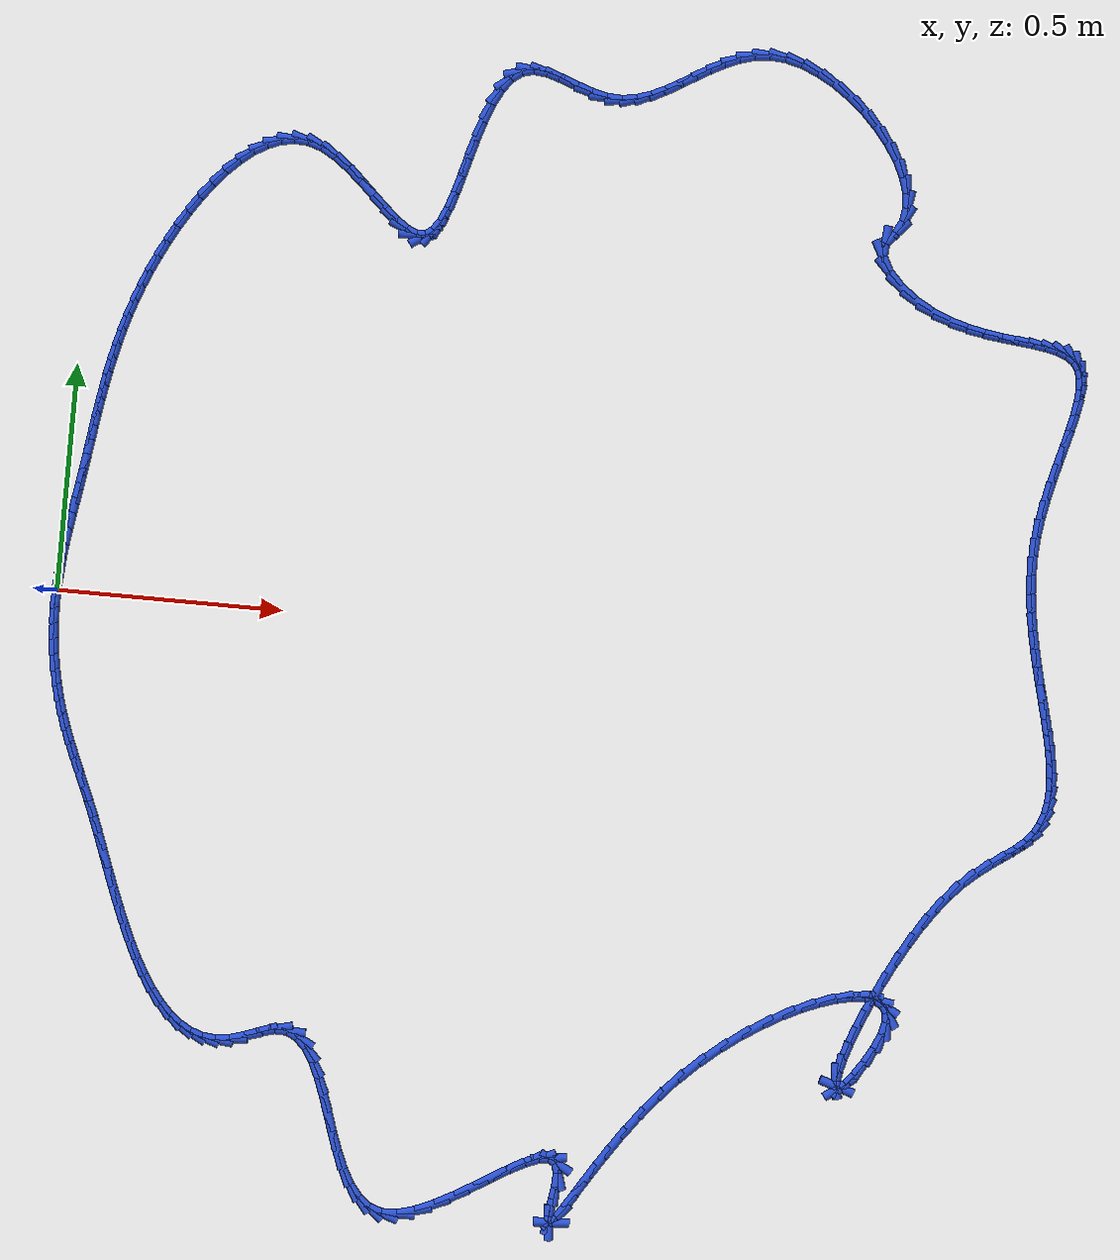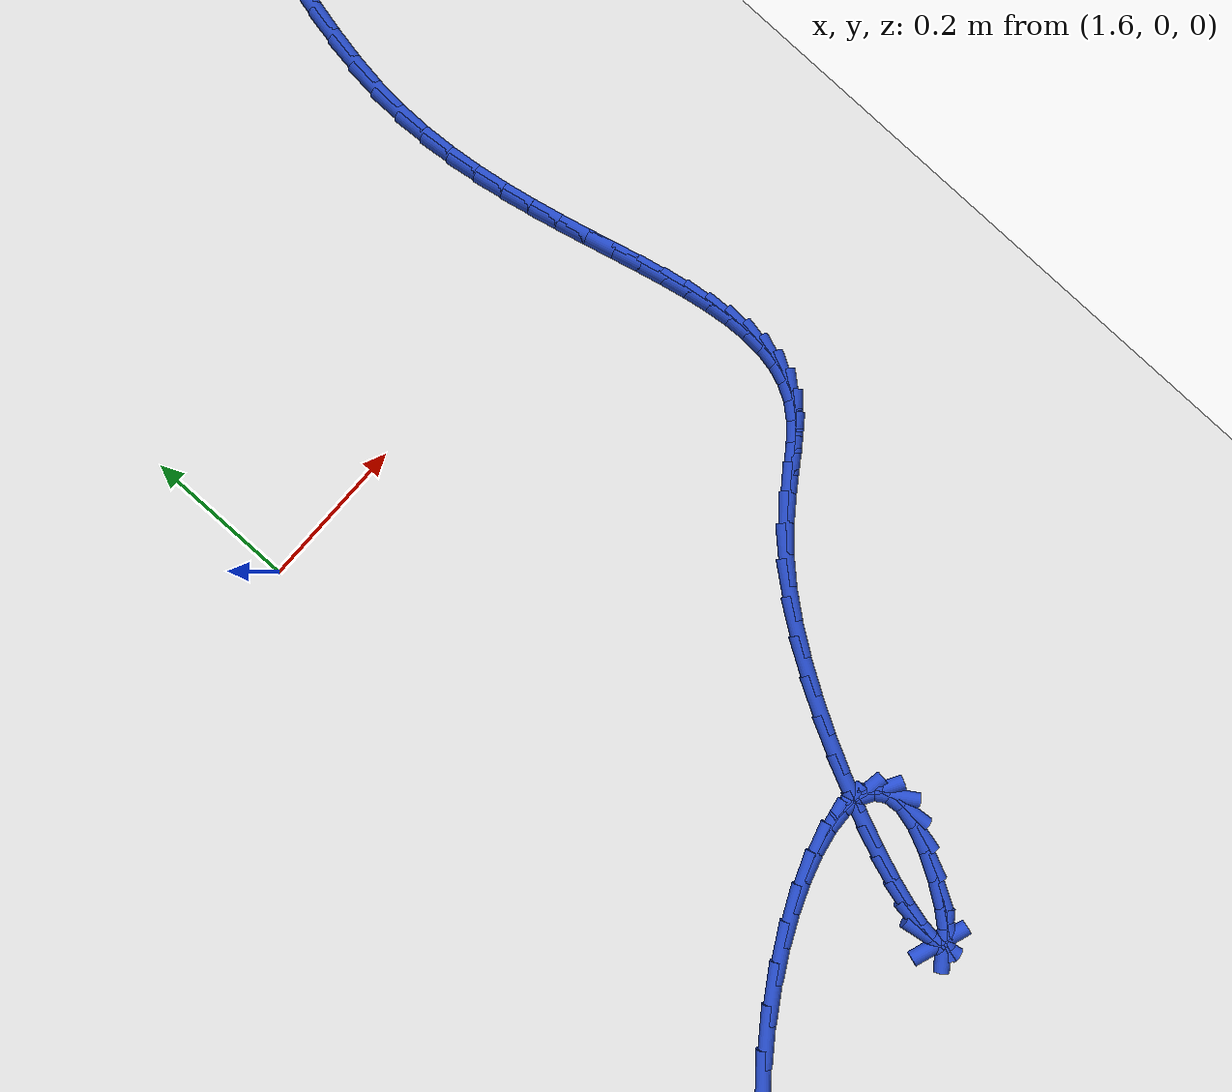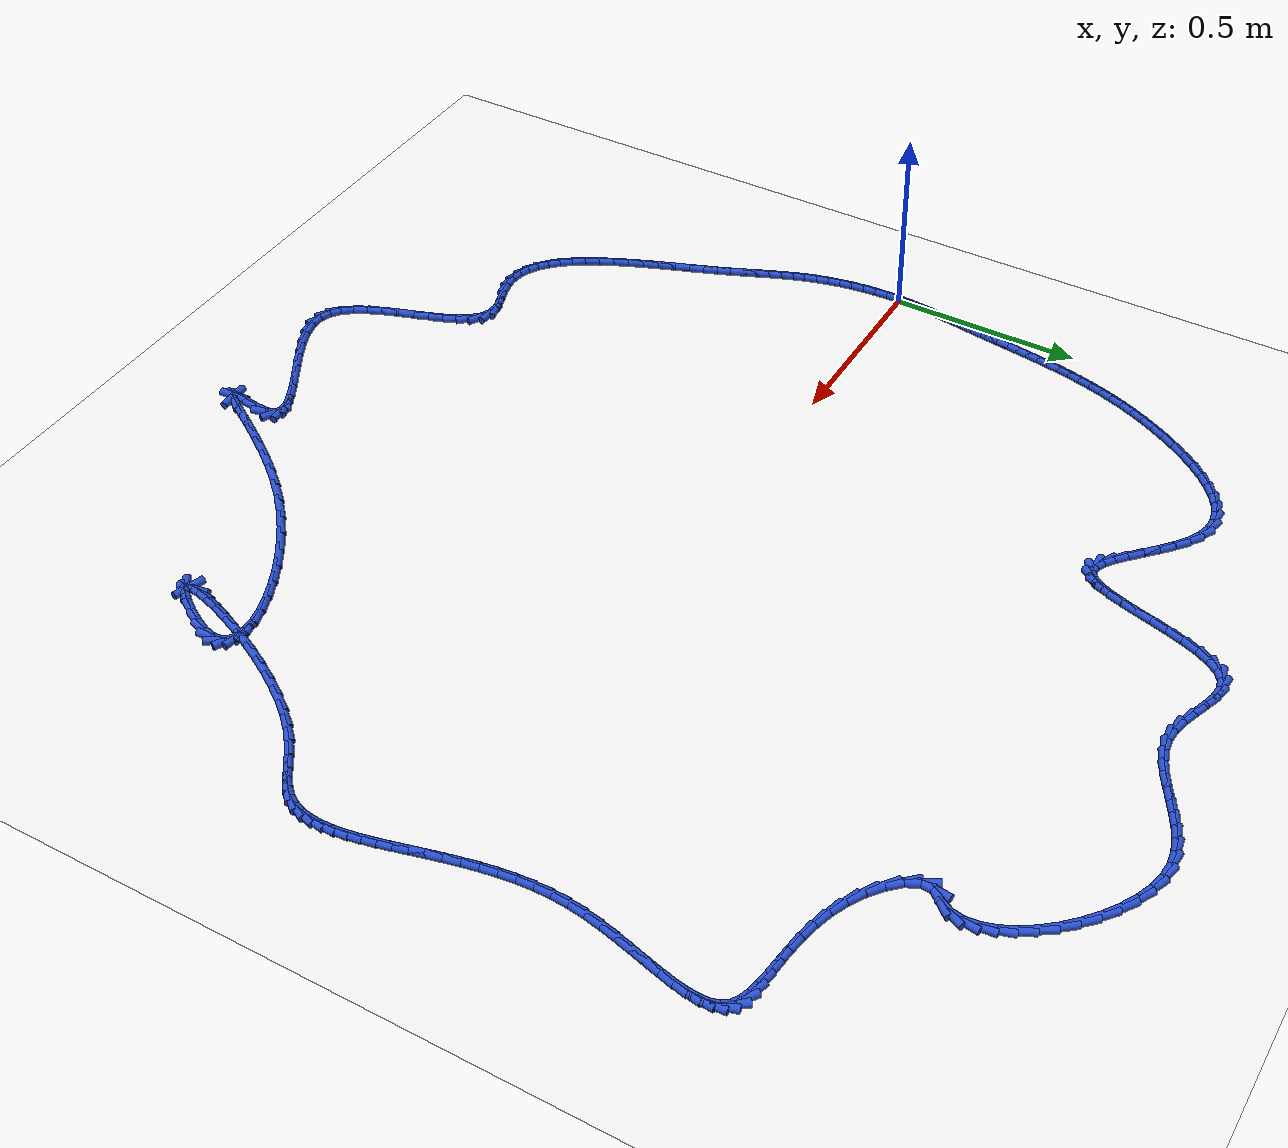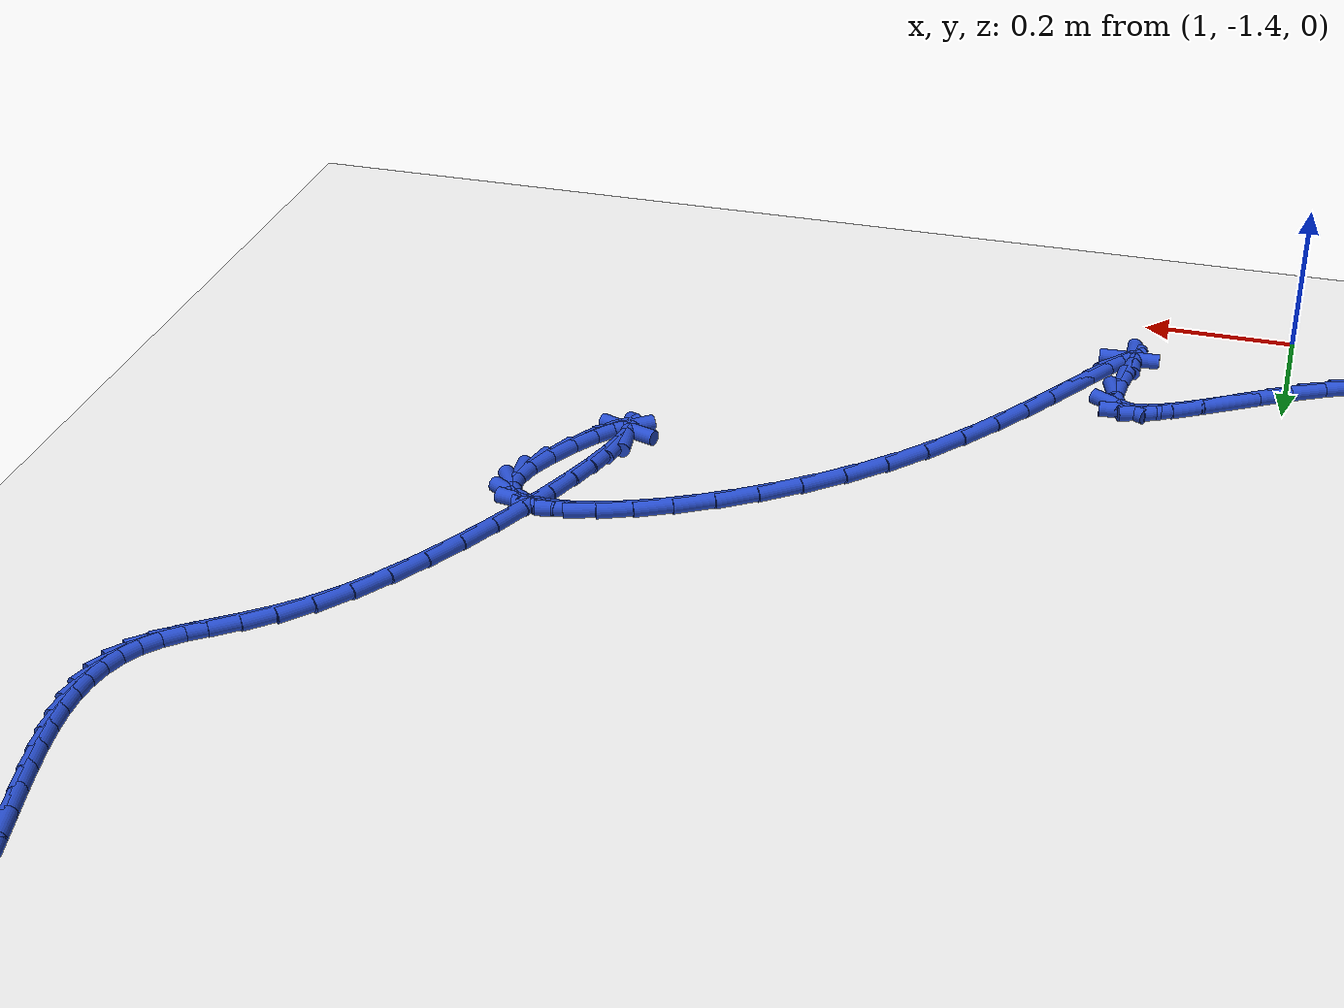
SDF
<sdf version="1.6">
 <world name="default">
  <light name="sun" type="directional">
   <pose>0 0 10 0 -0 0</pose>
   <diffuse>0.8 0.8 0.8 1</diffuse>
   <specular>0.2 0.2 0.2 1</specular>
   <attenuation>
    <range>1000</range>
    <constant>0.9</constant>
    <linear>0.01</linear>
    <quadratic>0.001</quadratic>
   </attenuation>
   <direction>-0.5 0.1 -0.9</direction>
  </light>
  <model name="ground_plane">
   <static>1</static>
   <link name="link">
    <collision name="collision">
     <geometry><plane><normal>0 0 1</normal><size>100 100</size></plane></geometry>
     <surface><friction><ode><mu>100</mu><mu2>50</mu2></ode></friction></surface>
    </collision>
    <visual name="visual">
     <cast_shadows>0</cast_shadows>
     <geometry><plane><normal>0 0 1</normal><size>100 100</size></plane></geometry>
     <material>
      <script><uri>file://media/materials/scripts/gazebo.material</uri><name>Gazebo/WhiteGlow</name></script>
     </material>
    </visual>
   </link>
  </model>
  <gravity>0 0 -9.8</gravity>
  <magnetic_field>6e-06 2.3e-05 -4.2e-05</magnetic_field>
  <atmosphere type="adiabatic"/>
  <physics name="default_physics" default="0" type="ode">
   <max_step_size>0.001</max_step_size>
   <real_time_factor>1</real_time_factor>
   <real_time_update_rate>1000</real_time_update_rate>
  </physics>
  <scene><ambient>0.4 0.4 0.4 1</ambient><background>0.7 0.7 0.7 1</background><shadows>1</shadows></scene>
  <spherical_coordinates>
   <surface_model>EARTH_WGS84</surface_model>
   <latitude_deg>0</latitude_deg>
   <longitude_deg>0</longitude_deg>
   <elevation>0</elevation>
   <heading_deg>0</heading_deg>
  </spherical_coordinates>
  <model name="line">
   <link name="link_0">
    <pose>-1.5612511283791264e-17 2.7755575615628914e-17 0.01 0 1.57 1.520571812726216</pose>
    <collision name="collision">
     <geometry><cylinder><radius>0.01</radius><length>0.08</length></cylinder></geometry>
    </collision>
    <visual name="visual">
     <material>
      <script><name>Gazebo/Blue</name><uri>file://media/materials/scripts/gazebo.material</uri></script>
     </material>
     <geometry><cylinder><radius>0.01</radius><length>0.08</length></cylinder></geometry>
    </visual>
   </link>
   <link name="link_1">
    <pose>0.0017129575458221964 0.03407732304532035 0.01 0 1.57 1.4842601919959186</pose>
    <collision name="collision">
     <geometry><cylinder><radius>0.01</radius><length>0.08</length></cylinder></geometry>
    </collision>
    <visual name="visual">
     <material>
      <script><name>Gazebo/Blue</name><uri>file://media/materials/scripts/gazebo.material</uri></script>
     </material>
     <geometry><cylinder><radius>0.01</radius><length>0.08</length></cylinder></geometry>
    </visual>
   </link>
   <link name="link_2">
    <pose>0.0046525323501623176 0.06796182082317884 0.01 0 1.57 1.4549711656289155</pose>
    <collision name="collision">
     <geometry><cylinder><radius>0.01</radius><length>0.08</length></cylinder></geometry>
    </collision>
    <visual name="visual">
     <material>
      <script><name>Gazebo/Blue</name><uri>file://media/materials/scripts/gazebo.material</uri></script>
     </material>
     <geometry><cylinder><radius>0.01</radius><length>0.08</length></cylinder></geometry>
    </visual>
   </link>
   <link name="link_3">
    <pose>0.008570992994723099 0.10164122392108339 0.01 0 1.57 1.43272845077841</pose>
    <collision name="collision">
     <geometry><cylinder><radius>0.01</radius><length>0.08</length></cylinder></geometry>
    </collision>
    <visual name="visual">
     <material>
      <script><name>Gazebo/Blue</name><uri>file://media/materials/scripts/gazebo.material</uri></script>
     </material>
     <geometry><cylinder><radius>0.01</radius><length>0.08</length></cylinder></geometry>
    </visual>
   </link>
   <link name="link_4">
    <pose>0.01322060806120728 0.13510326292654193 0.01 0 1.57 1.4175485551472882</pose>
    <collision name="collision">
     <geometry><cylinder><radius>0.01</radius><length>0.08</length></cylinder></geometry>
    </collision>
    <visual name="visual">
     <material>
      <script><name>Gazebo/Blue</name><uri>file://media/materials/scripts/gazebo.material</uri></script>
     </material>
     <geometry><cylinder><radius>0.01</radius><length>0.08</length></cylinder></geometry>
    </visual>
   </link>
   <link name="link_5">
    <pose>0.01835364613131762 0.16833566842706235 0.01 0 1.57 1.4094748795809577</pose>
    <collision name="collision">
     <geometry><cylinder><radius>0.01</radius><length>0.08</length></cylinder></geometry>
    </collision>
    <visual name="visual">
     <material>
      <script><name>Gazebo/Blue</name><uri>file://media/materials/scripts/gazebo.material</uri></script>
     </material>
     <geometry><cylinder><radius>0.01</radius><length>0.08</length></cylinder></geometry>
    </visual>
   </link>
   <link name="link_6">
    <pose>0.02372237578675685 0.2013261710101525 0.01 0 1.57 1.4086023789277209</pose>
    <collision name="collision">
     <geometry><cylinder><radius>0.01</radius><length>0.08</length></cylinder></geometry>
    </collision>
    <visual name="visual">
     <material>
      <script><name>Gazebo/Blue</name><uri>file://media/materials/scripts/gazebo.material</uri></script>
     </material>
     <geometry><cylinder><radius>0.01</radius><length>0.08</length></cylinder></geometry>
    </visual>
   </link>
   <link name="link_7">
    <pose>0.029079065609227732 0.23406250126332023 0.01 0 1.57 1.4147755472724906</pose>
    <collision name="collision">
     <geometry><cylinder><radius>0.01</radius><length>0.08</length></cylinder></geometry>
    </collision>
    <visual name="visual">
     <material>
      <script><name>Gazebo/Blue</name><uri>file://media/materials/scripts/gazebo.material</uri></script>
     </material>
     <geometry><cylinder><radius>0.01</radius><length>0.08</length></cylinder></geometry>
    </visual>
   </link>
   <link name="link_8">
    <pose>0.03418682468213099 0.2665341149353378 0.01 0 1.57 1.422314649603854</pose>
    <collision name="collision">
     <geometry><cylinder><radius>0.01</radius><length>0.08</length></cylinder></geometry>
    </collision>
    <visual name="visual">
     <material>
      <script><name>Gazebo/Blue</name><uri>file://media/materials/scripts/gazebo.material</uri></script>
     </material>
     <geometry><cylinder><radius>0.01</radius><length>0.08</length></cylinder></geometry>
    </visual>
   </link>
   <link name="link_9">
    <pose>0.03900757041063666 0.2987621062014356 0.01 0 1.57 1.4260335351261257</pose>
    <collision name="collision">
     <geometry><cylinder><radius>0.01</radius><length>0.08</length></cylinder></geometry>
    </collision>
    <visual name="visual">
     <material>
      <script><name>Gazebo/Blue</name><uri>file://media/materials/scripts/gazebo.material</uri></script>
     </material>
     <geometry><cylinder><radius>0.01</radius><length>0.08</length></cylinder></geometry>
    </visual>
   </link>
   <link name="link_10">
    <pose>0.04367745120620504 0.33079529642064714 0.01 0 1.57 1.4256550575435196</pose>
    <collision name="collision">
     <geometry><cylinder><radius>0.01</radius><length>0.08</length></cylinder></geometry>
    </collision>
    <visual name="visual">
     <material>
      <script><name>Gazebo/Blue</name><uri>file://media/materials/scripts/gazebo.material</uri></script>
     </material>
     <geometry><cylinder><radius>0.01</radius><length>0.08</length></cylinder></geometry>
    </visual>
   </link>
   <link name="link_11">
    <pose>0.048338513671441825 0.36268344559222543 0.01 0 1.57 1.4211263439757893</pose>
    <collision name="collision">
     <geometry><cylinder><radius>0.01</radius><length>0.08</length></cylinder></geometry>
    </collision>
    <visual name="visual">
     <material>
      <script><name>Gazebo/Blue</name><uri>file://media/materials/scripts/gazebo.material</uri></script>
     </material>
     <geometry><cylinder><radius>0.01</radius><length>0.08</length></cylinder></geometry>
    </visual>
   </link>
   <link name="link_12">
    <pose>0.053132804408952745 0.39447631371542347 0.01 0 1.57 1.4124485089330339</pose>
    <collision name="collision">
     <geometry><cylinder><radius>0.01</radius><length>0.08</length></cylinder></geometry>
    </collision>
    <visual name="visual">
     <material>
      <script><name>Gazebo/Blue</name><uri>file://media/materials/scripts/gazebo.material</uri></script>
     </material>
     <geometry><cylinder><radius>0.01</radius><length>0.08</length></cylinder></geometry>
    </visual>
   </link>
   <link name="link_13">
    <pose>0.058202370021343514 0.4262236607894941 0.01 0 1.57 1.3996795672735154</pose>
    <collision name="collision">
     <geometry><cylinder><radius>0.01</radius><length>0.08</length></cylinder></geometry>
    </collision>
    <visual name="visual">
     <material>
      <script><name>Gazebo/Blue</name><uri>file://media/materials/scripts/gazebo.material</uri></script>
     </material>
     <geometry><cylinder><radius>0.01</radius><length>0.08</length></cylinder></geometry>
    </visual>
   </link>
   <link name="link_14">
    <pose>0.06368925711121982 0.45797524681369034 0.01 0 1.57 1.382937457638164</pose>
    <collision name="collision">
     <geometry><cylinder><radius>0.01</radius><length>0.08</length></cylinder></geometry>
    </collision>
    <visual name="visual">
     <material>
      <script><name>Gazebo/Blue</name><uri>file://media/materials/scripts/gazebo.material</uri></script>
     </material>
     <geometry><cylinder><radius>0.01</radius><length>0.08</length></cylinder></geometry>
    </visual>
   </link>
   <link name="link_15">
    <pose>0.06973551228118738 0.4897808317872651 0.01 0 1.57 1.3624026111968137</pose>
    <collision name="collision">
     <geometry><cylinder><radius>0.01</radius><length>0.08</length></cylinder></geometry>
    </collision>
    <visual name="visual">
     <material>
      <script><name>Gazebo/Blue</name><uri>file://media/materials/scripts/gazebo.material</uri></script>
     </material>
     <geometry><cylinder><radius>0.01</radius><length>0.08</length></cylinder></geometry>
    </visual>
   </link>
   <link name="link_16">
    <pose>0.07648318213385195 0.5216901757094716 0.01 0 1.57 1.3383192652040032</pose>
    <collision name="collision">
     <geometry><cylinder><radius>0.01</radius><length>0.08</length></cylinder></geometry>
    </collision>
    <visual name="visual">
     <material>
      <script><name>Gazebo/Blue</name><uri>file://media/materials/scripts/gazebo.material</uri></script>
     </material>
     <geometry><cylinder><radius>0.01</radius><length>0.08</length></cylinder></geometry>
    </visual>
   </link>
   <link name="link_17">
    <pose>0.08407431327181922 0.5537530385795626 0.01 0 1.57 1.310994596529873</pose>
    <collision name="collision">
     <geometry><cylinder><radius>0.01</radius><length>0.08</length></cylinder></geometry>
    </collision>
    <visual name="visual">
     <material>
      <script><name>Gazebo/Blue</name><uri>file://media/materials/scripts/gazebo.material</uri></script>
     </material>
     <geometry><cylinder><radius>0.01</radius><length>0.08</length></cylinder></geometry>
    </visual>
   </link>
   <link name="link_18">
    <pose>0.09265095229769488 0.5860191803967912 0.01 0 1.57 1.2807947972817584</pose>
    <collision name="collision">
     <geometry><cylinder><radius>0.01</radius><length>0.08</length></cylinder></geometry>
    </collision>
    <visual name="visual">
     <material>
      <script><name>Gazebo/Blue</name><uri>file://media/materials/scripts/gazebo.material</uri></script>
     </material>
     <geometry><cylinder><radius>0.01</radius><length>0.08</length></cylinder></geometry>
    </visual>
   </link>
   <link name="link_19">
    <pose>0.10235514581408464 0.6185383611604103 0.01 0 1.57 1.2481374725647716</pose>
    <collision name="collision">
     <geometry><cylinder><radius>0.01</radius><length>0.08</length></cylinder></geometry>
    </collision>
    <visual name="visual">
     <material>
      <script><name>Gazebo/Blue</name><uri>file://media/materials/scripts/gazebo.material</uri></script>
     </material>
     <geometry><cylinder><radius>0.01</radius><length>0.08</length></cylinder></geometry>
    </visual>
   </link>
   <link name="link_20">
    <pose>0.11332894042359427 0.6513603408696728 0.01 0 1.57 1.2134802041225186</pose>
    <collision name="collision">
     <geometry><cylinder><radius>0.01</radius><length>0.08</length></cylinder></geometry>
    </collision>
    <visual name="visual">
     <material>
      <script><name>Gazebo/Blue</name><uri>file://media/materials/scripts/gazebo.material</uri></script>
     </material>
     <geometry><cylinder><radius>0.01</radius><length>0.08</length></cylinder></geometry>
    </visual>
   </link>
   <link name="link_21">
    <pose>0.12571438272882945 0.6845348795238321 0.01 0 1.57 1.177305725559883</pose>
    <collision name="collision">
     <geometry><cylinder><radius>0.01</radius><length>0.08</length></cylinder></geometry>
    </collision>
    <visual name="visual">
     <material>
      <script><name>Gazebo/Blue</name><uri>file://media/materials/scripts/gazebo.material</uri></script>
     </material>
     <geometry><cylinder><radius>0.01</radius><length>0.08</length></cylinder></geometry>
    </visual>
   </link>
   <link name="link_22">
    <pose>0.13965351933239586 0.7181117371221403 0.01 0 1.57 1.140104768636265</pose>
    <collision name="collision">
     <geometry><cylinder><radius>0.01</radius><length>0.08</length></cylinder></geometry>
    </collision>
    <visual name="visual">
     <material>
      <script><name>Gazebo/Blue</name><uri>file://media/materials/scripts/gazebo.material</uri></script>
     </material>
     <geometry><cylinder><radius>0.01</radius><length>0.08</length></cylinder></geometry>
    </visual>
   </link>
   <link name="link_23">
    <pose>0.1552883968368993 0.7521406736638514 0.01 0 1.57 1.1023581114921528</pose>
    <collision name="collision">
     <geometry><cylinder><radius>0.01</radius><length>0.08</length></cylinder></geometry>
    </collision>
    <visual name="visual">
     <material>
      <script><name>Gazebo/Blue</name><uri>file://media/materials/scripts/gazebo.material</uri></script>
     </material>
     <geometry><cylinder><radius>0.01</radius><length>0.08</length></cylinder></geometry>
    </visual>
   </link>
   <link name="link_24">
    <pose>0.1727610618449454 0.7866714491482176 0.01 0 1.57 1.0641385668596526</pose>
    <collision name="collision">
     <geometry><cylinder><radius>0.01</radius><length>0.08</length></cylinder></geometry>
    </collision>
    <visual name="visual">
     <material>
      <script><name>Gazebo/Blue</name><uri>file://media/materials/scripts/gazebo.material</uri></script>
     </material>
     <geometry><cylinder><radius>0.01</radius><length>0.08</length></cylinder></geometry>
    </visual>
   </link>
   <link name="link_25">
    <pose>0.19218164993746326 0.8216648288823318 0.01 0 1.57 1.022818600783752</pose>
    <collision name="collision">
     <geometry><cylinder><radius>0.01</radius><length>0.08</length></cylinder></geometry>
    </collision>
    <visual name="visual">
     <material>
      <script><name>Gazebo/Blue</name><uri>file://media/materials/scripts/gazebo.material</uri></script>
     </material>
     <geometry><cylinder><radius>0.01</radius><length>0.08</length></cylinder></geometry>
    </visual>
   </link>
   <link name="link_26">
    <pose>0.21346499200235272 0.8565369048873673 0.01 0 1.57 0.9757638037013268</pose>
    <collision name="collision">
     <geometry><cylinder><radius>0.01</radius><length>0.08</length></cylinder></geometry>
    </collision>
    <visual name="visual">
     <material>
      <script><name>Gazebo/Blue</name><uri>file://media/materials/scripts/gazebo.material</uri></script>
     </material>
     <geometry><cylinder><radius>0.01</radius><length>0.08</length></cylinder></geometry>
    </visual>
   </link>
   <link name="link_27">
    <pose>0.23645205933200503 0.8904977866862875 0.01 0 1.57 0.920641556662598</pose>
    <collision name="collision">
     <geometry><cylinder><radius>0.01</radius><length>0.08</length></cylinder></geometry>
    </collision>
    <visual name="visual">
     <material>
      <script><name>Gazebo/Blue</name><uri>file://media/materials/scripts/gazebo.material</uri></script>
     </material>
     <geometry><cylinder><radius>0.01</radius><length>0.08</length></cylinder></geometry>
    </visual>
   </link>
   <link name="link_28">
    <pose>0.26098368492149704 0.9227571981131536 0.01 0 1.57 0.854439194632769</pose>
    <collision name="collision">
     <geometry><cylinder><radius>0.01</radius><length>0.08</length></cylinder></geometry>
    </collision>
    <visual name="visual">
     <material>
      <script><name>Gazebo/Blue</name><uri>file://media/materials/scripts/gazebo.material</uri></script>
     </material>
     <geometry><cylinder><radius>0.01</radius><length>0.08</length></cylinder></geometry>
    </visual>
   </link>
   <link name="link_29">
    <pose>0.28690070176590543 0.9525248630020261 0.01 0 1.57 0.773136749138018</pose>
    <collision name="collision">
     <geometry><cylinder><radius>0.01</radius><length>0.08</length></cylinder></geometry>
    </collision>
    <visual name="visual">
     <material>
      <script><name>Gazebo/Blue</name><uri>file://media/materials/scripts/gazebo.material</uri></script>
     </material>
     <geometry><cylinder><radius>0.01</radius><length>0.08</length></cylinder></geometry>
    </visual>
   </link>
   <link name="link_30">
    <pose>0.31404394286030674 0.9790105051869654 0.01 0 1.57 0.6713839524461769</pose>
    <collision name="collision">
     <geometry><cylinder><radius>0.01</radius><length>0.08</length></cylinder></geometry>
    </collision>
    <visual name="visual">
     <material>
      <script><name>Gazebo/Blue</name><uri>file://media/materials/scripts/gazebo.material</uri></script>
     </material>
     <geometry><cylinder><radius>0.01</radius><length>0.08</length></cylinder></geometry>
    </visual>
   </link>
   <link name="link_31">
    <pose>0.342254241199778 1.001423848502033 0.01 0 1.57 0.5424335669392112</pose>
    <collision name="collision">
     <geometry><cylinder><radius>0.01</radius><length>0.08</length></cylinder></geometry>
    </collision>
    <visual name="visual">
     <material>
      <script><name>Gazebo/Blue</name><uri>file://media/materials/scripts/gazebo.material</uri></script>
     </material>
     <geometry><cylinder><radius>0.01</radius><length>0.08</length></cylinder></geometry>
    </visual>
   </link>
   <link name="link_32">
    <pose>0.37137242977939566 1.0189746167812892 0.01 0 1.57 0.3790956595856606</pose>
    <collision name="collision">
     <geometry><cylinder><radius>0.01</radius><length>0.08</length></cylinder></geometry>
    </collision>
    <visual name="visual">
     <material>
      <script><name>Gazebo/Blue</name><uri>file://media/materials/scripts/gazebo.material</uri></script>
     </material>
     <geometry><cylinder><radius>0.01</radius><length>0.08</length></cylinder></geometry>
    </visual>
   </link>
   <link name="link_33">
    <pose>0.4012393415942365 1.0308725338587945 0.01 0 1.57 0.17722220078351983</pose>
    <collision name="collision">
     <geometry><cylinder><radius>0.01</radius><length>0.08</length></cylinder></geometry>
    </collision>
    <visual name="visual">
     <material>
      <script><name>Gazebo/Blue</name><uri>file://media/materials/scripts/gazebo.material</uri></script>
     </material>
     <geometry><cylinder><radius>0.01</radius><length>0.08</length></cylinder></geometry>
    </visual>
   </link>
   <link name="link_34">
    <pose>0.4316958096393773 1.0363273235686101 0.01 0 1.57 -0.05752128626095289</pose>
    <collision name="collision">
     <geometry><cylinder><radius>0.01</radius><length>0.08</length></cylinder></geometry>
    </collision>
    <visual name="visual">
     <material>
      <script><name>Gazebo/Blue</name><uri>file://media/materials/scripts/gazebo.material</uri></script>
     </material>
     <geometry><cylinder><radius>0.01</radius><length>0.08</length></cylinder></geometry>
    </visual>
   </link>
   <link name="link_35">
    <pose>0.4625826669098947 1.0345487097447967 0.01 0 1.57 -0.3045049238478764</pose>
    <collision name="collision">
     <geometry><cylinder><radius>0.01</radius><length>0.08</length></cylinder></geometry>
    </collision>
    <visual name="visual">
     <material>
      <script><name>Gazebo/Blue</name><uri>file://media/materials/scripts/gazebo.material</uri></script>
     </material>
     <geometry><cylinder><radius>0.01</radius><length>0.08</length></cylinder></geometry>
    </visual>
   </link>
   <link name="link_36">
    <pose>0.49374016635433005 1.024756556795236 0.01 0 1.57 -0.5129059545784163</pose>
    <collision name="collision">
     <geometry><cylinder><radius>0.01</radius><length>0.08</length></cylinder></geometry>
    </collision>
    <visual name="visual">
     <material>
      <script><name>Gazebo/Blue</name><uri>file://media/materials/scripts/gazebo.material</uri></script>
     </material>
     <geometry><cylinder><radius>0.01</radius><length>0.08</length></cylinder></geometry>
    </visual>
   </link>
   <link name="link_37">
    <pose>0.5249508695610515 1.0071793094072925 0.01 0 1.57 -0.6450991111193133</pose>
    <collision name="collision">
     <geometry><cylinder><radius>0.01</radius><length>0.08</length></cylinder></geometry>
    </collision>
    <visual name="visual">
     <material>
      <script><name>Gazebo/Blue</name><uri>file://media/materials/scripts/gazebo.material</uri></script>
     </material>
     <geometry><cylinder><radius>0.01</radius><length>0.08</length></cylinder></geometry>
    </visual>
   </link>
   <link name="link_38">
    <pose>0.555891453495628 0.9838965238062652 0.01 0 1.57 -0.7219313332146254</pose>
    <collision name="collision">
     <geometry><cylinder><radius>0.01</radius><length>0.08</length></cylinder></geometry>
    </collision>
    <visual name="visual">
     <material>
      <script><name>Gazebo/Blue</name><uri>file://media/materials/scripts/gazebo.material</uri></script>
     </material>
     <geometry><cylinder><radius>0.01</radius><length>0.08</length></cylinder></geometry>
    </visual>
   </link>
   <link name="link_39">
    <pose>0.5862272475167218 0.9571861389997451 0.01 0 1.57 -0.7585728562040256</pose>
    <collision name="collision">
     <geometry><cylinder><radius>0.01</radius><length>0.08</length></cylinder></geometry>
    </collision>
    <visual name="visual">
     <material>
      <script><name>Gazebo/Blue</name><uri>file://media/materials/scripts/gazebo.material</uri></script>
     </material>
     <geometry><cylinder><radius>0.01</radius><length>0.08</length></cylinder></geometry>
    </visual>
   </link>
   <link name="link_40">
    <pose>0.615623580982995 0.9293260939953212 0.01 0 1.57 -0.7600556323977313</pose>
    <collision name="collision">
     <geometry><cylinder><radius>0.01</radius><length>0.08</length></cylinder></geometry>
    </collision>
    <visual name="visual">
     <material>
      <script><name>Gazebo/Blue</name><uri>file://media/materials/scripts/gazebo.material</uri></script>
     </material>
     <geometry><cylinder><radius>0.01</radius><length>0.08</length></cylinder></geometry>
    </visual>
   </link>
   <link name="link_41">
    <pose>0.6437457832531096 0.9025943278005825 0.01 0 1.57 -0.7215221123712428</pose>
    <collision name="collision">
     <geometry><cylinder><radius>0.01</radius><length>0.08</length></cylinder></geometry>
    </collision>
    <visual name="visual">
     <material>
      <script><name>Gazebo/Blue</name><uri>file://media/materials/scripts/gazebo.material</uri></script>
     </material>
     <geometry><cylinder><radius>0.01</radius><length>0.08</length></cylinder></geometry>
    </visual>
   </link>
   <link name="link_42">
    <pose>0.6702591836857283 0.87926877942312 0.01 0 1.57 -0.6227095495214341</pose>
    <collision name="collision">
     <geometry><cylinder><radius>0.01</radius><length>0.08</length></cylinder></geometry>
    </collision>
    <visual name="visual">
     <material>
      <script><name>Gazebo/Blue</name><uri>file://media/materials/scripts/gazebo.material</uri></script>
     </material>
     <geometry><cylinder><radius>0.01</radius><length>0.08</length></cylinder></geometry>
    </visual>
   </link>
   <link name="link_43">
    <pose>0.6948291116395129 0.8616273878705222 0.01 0 1.57 -0.409644904419674</pose>
    <collision name="collision">
     <geometry><cylinder><radius>0.01</radius><length>0.08</length></cylinder></geometry>
    </collision>
    <visual name="visual">
     <material>
      <script><name>Gazebo/Blue</name><uri>file://media/materials/scripts/gazebo.material</uri></script>
     </material>
     <geometry><cylinder><radius>0.01</radius><length>0.08</length></cylinder></geometry>
    </visual>
   </link>
   <link name="link_44">
    <pose>0.7171208964731258 0.8519480921503794 0.01 0 1.57 0.027998202393448315</pose>
    <collision name="collision">
     <geometry><cylinder><radius>0.01</radius><length>0.08</length></cylinder></geometry>
    </collision>
    <visual name="visual">
     <material>
      <script><name>Gazebo/Blue</name><uri>file://media/materials/scripts/gazebo.material</uri></script>
     </material>
     <geometry><cylinder><radius>0.01</radius><length>0.08</length></cylinder></geometry>
    </visual>
   </link>
   <link name="link_45">
    <pose>0.736801901212656 0.8524992689342822 0.01 0 1.57 0.6056768249851149</pose>
    <collision name="collision">
     <geometry><cylinder><radius>0.01</radius><length>0.08</length></cylinder></geometry>
    </collision>
    <visual name="visual">
     <material>
      <script><name>Gazebo/Blue</name><uri>file://media/materials/scripts/gazebo.material</uri></script>
     </material>
     <geometry><cylinder><radius>0.01</radius><length>0.08</length></cylinder></geometry>
    </visual>
   </link>
   <link name="link_46">
    <pose>0.753809984312621 0.8642774211653742 0.01 0 1.57 0.9668228177981564</pose>
    <collision name="collision">
     <geometry><cylinder><radius>0.01</radius><length>0.08</length></cylinder></geometry>
    </collision>
    <visual name="visual">
     <material>
      <script><name>Gazebo/Blue</name><uri>file://media/materials/scripts/gazebo.material</uri></script>
     </material>
     <geometry><cylinder><radius>0.01</radius><length>0.08</length></cylinder></geometry>
    </visual>
   </link>
   <link name="link_47">
    <pose>0.7686220227294884 0.8857445783734633 0.01 0 1.57 1.148971528005886</pose>
    <collision name="collision">
     <geometry><cylinder><radius>0.01</radius><length>0.08</length></cylinder></geometry>
    </collision>
    <visual name="visual">
     <material>
      <script><name>Gazebo/Blue</name><uri>file://media/materials/scripts/gazebo.material</uri></script>
     </material>
     <geometry><cylinder><radius>0.01</radius><length>0.08</length></cylinder></geometry>
    </visual>
   </link>
   <link name="link_48">
    <pose>0.781778775561127 0.9150623952619275 0.01 0 1.57 1.242297335673481</pose>
    <collision name="collision">
     <geometry><cylinder><radius>0.01</radius><length>0.08</length></cylinder></geometry>
    </collision>
    <visual name="visual">
     <material>
      <script><name>Gazebo/Blue</name><uri>file://media/materials/scripts/gazebo.material</uri></script>
     </material>
     <geometry><cylinder><radius>0.01</radius><length>0.08</length></cylinder></geometry>
    </visual>
   </link>
   <link name="link_49">
    <pose>0.7938210019054054 0.9503925265341445 0.01 0 1.57 1.288252426560456</pose>
    <collision name="collision">
     <geometry><cylinder><radius>0.01</radius><length>0.08</length></cylinder></geometry>
    </collision>
    <visual name="visual">
     <material>
      <script><name>Gazebo/Blue</name><uri>file://media/materials/scripts/gazebo.material</uri></script>
     </material>
     <geometry><cylinder><radius>0.01</radius><length>0.08</length></cylinder></geometry>
    </visual>
   </link>
   <link name="link_50">
    <pose>0.8052894608601919 0.9898966268934922 0.01 0 1.57 1.3039967324472017</pose>
    <collision name="collision">
     <geometry><cylinder><radius>0.01</radius><length>0.08</length></cylinder></geometry>
    </collision>
    <visual name="visual">
     <material>
      <script><name>Gazebo/Blue</name><uri>file://media/materials/scripts/gazebo.material</uri></script>
     </material>
     <geometry><cylinder><radius>0.01</radius><length>0.08</length></cylinder></geometry>
    </visual>
   </link>
   <link name="link_51">
    <pose>0.8167249115233552 1.0317363510433484 0.01 0 1.57 1.295842823364231</pose>
    <collision name="collision">
     <geometry><cylinder><radius>0.01</radius><length>0.08</length></cylinder></geometry>
    </collision>
    <visual name="visual">
     <material>
      <script><name>Gazebo/Blue</name><uri>file://media/materials/scripts/gazebo.material</uri></script>
     </material>
     <geometry><cylinder><radius>0.01</radius><length>0.08</length></cylinder></geometry>
    </visual>
   </link>
   <link name="link_52">
    <pose>0.828668112992764 1.0740733536870914 0.01 0 1.57 1.263905752716108</pose>
    <collision name="collision">
     <geometry><cylinder><radius>0.01</radius><length>0.08</length></cylinder></geometry>
    </collision>
    <visual name="visual">
     <material>
      <script><name>Gazebo/Blue</name><uri>file://media/materials/scripts/gazebo.material</uri></script>
     </material>
     <geometry><cylinder><radius>0.01</radius><length>0.08</length></cylinder></geometry>
    </visual>
   </link>
   <link name="link_53">
    <pose>0.8416598243662866 1.115069289528098 0.01 0 1.57 1.2027897035171078</pose>
    <collision name="collision">
     <geometry><cylinder><radius>0.01</radius><length>0.08</length></cylinder></geometry>
    </collision>
    <visual name="visual">
     <material>
      <script><name>Gazebo/Blue</name><uri>file://media/materials/scripts/gazebo.material</uri></script>
     </material>
     <geometry><cylinder><radius>0.01</radius><length>0.08</length></cylinder></geometry>
    </visual>
   </link>
   <link name="link_54">
    <pose>0.8562408047417918 1.1528858132697468 0.01 0 1.57 1.0995767369907883</pose>
    <collision name="collision">
     <geometry><cylinder><radius>0.01</radius><length>0.08</length></cylinder></geometry>
    </collision>
    <visual name="visual">
     <material>
      <script><name>Gazebo/Blue</name><uri>file://media/materials/scripts/gazebo.material</uri></script>
     </material>
     <geometry><cylinder><radius>0.01</radius><length>0.08</length></cylinder></geometry>
    </visual>
   </link>
   <link name="link_55">
    <pose>0.8729518132171481 1.1856845796154163 0.01 0 1.57 0.929153019846278</pose>
    <collision name="collision">
     <geometry><cylinder><radius>0.01</radius><length>0.08</length></cylinder></geometry>
    </collision>
    <visual name="visual">
     <material>
      <script><name>Gazebo/Blue</name><uri>file://media/materials/scripts/gazebo.material</uri></script>
     </material>
     <geometry><cylinder><radius>0.01</radius><length>0.08</length></cylinder></geometry>
    </visual>
   </link>
   <link name="link_56">
    <pose>0.8923336088902241 1.2116272432684831 0.01 0 1.57 0.6520349129590362</pose>
    <collision name="collision">
     <geometry><cylinder><radius>0.01</radius><length>0.08</length></cylinder></geometry>
    </collision>
    <visual name="visual">
     <material>
      <script><name>Gazebo/Blue</name><uri>file://media/materials/scripts/gazebo.material</uri></script>
     </material>
     <geometry><cylinder><radius>0.01</radius><length>0.08</length></cylinder></geometry>
    </visual>
   </link>
   <link name="link_57">
    <pose>0.914926950858888 1.2288754589323254 0.01 0 1.57 0.2528734939650738</pose>
    <collision name="collision">
     <geometry><cylinder><radius>0.01</radius><length>0.08</length></cylinder></geometry>
    </collision>
    <visual name="visual">
     <material>
      <script><name>Gazebo/Blue</name><uri>file://media/materials/scripts/gazebo.material</uri></script>
     </material>
     <geometry><cylinder><radius>0.01</radius><length>0.08</length></cylinder></geometry>
    </visual>
   </link>
   <link name="link_58">
    <pose>0.9412478402961745 1.2356769089318365 0.01 0 1.57 -0.10010734732079744</pose>
    <collision name="collision">
     <geometry><cylinder><radius>0.01</radius><length>0.08</length></cylinder></geometry>
    </collision>
    <visual name="visual">
     <material>
      <script><name>Gazebo/Blue</name><uri>file://media/materials/scripts/gazebo.material</uri></script>
     </material>
     <geometry><cylinder><radius>0.01</radius><length>0.08</length></cylinder></geometry>
    </visual>
   </link>
   <link name="link_59">
    <pose>0.9711224638908772 1.232676209089458 0.01 0 1.57 -0.28454793795680744</pose>
    <collision name="collision">
     <geometry><cylinder><radius>0.01</radius><length>0.08</length></cylinder></geometry>
    </collision>
    <visual name="visual">
     <material>
      <script><name>Gazebo/Blue</name><uri>file://media/materials/scripts/gazebo.material</uri></script>
     </material>
     <geometry><cylinder><radius>0.01</radius><length>0.08</length></cylinder></geometry>
    </visual>
   </link>
   <link name="link_60">
    <pose>1.0036128406277778 1.2231732676422435 0.01 0 1.57 -0.3528293460210405</pose>
    <collision name="collision">
     <geometry><cylinder><radius>0.01</radius><length>0.08</length></cylinder></geometry>
    </collision>
    <visual name="visual">
     <material>
      <script><name>Gazebo/Blue</name><uri>file://media/materials/scripts/gazebo.material</uri></script>
     </material>
     <geometry><cylinder><radius>0.01</radius><length>0.08</length></cylinder></geometry>
    </visual>
   </link>
   <link name="link_61">
    <pose>1.0377413120587524 1.210605862022813 0.01 0 1.57 -0.337135037643859</pose>
    <collision name="collision">
     <geometry><cylinder><radius>0.01</radius><length>0.08</length></cylinder></geometry>
    </collision>
    <visual name="visual">
     <material>
      <script><name>Gazebo/Blue</name><uri>file://media/materials/scripts/gazebo.material</uri></script>
     </material>
     <geometry><cylinder><radius>0.01</radius><length>0.08</length></cylinder></geometry>
    </visual>
   </link>
   <link name="link_62">
    <pose>1.0725302197356754 1.198411769663786 0.01 0 1.57 -0.23855446451380014</pose>
    <collision name="collision">
     <geometry><cylinder><radius>0.01</radius><length>0.08</length></cylinder></geometry>
    </collision>
    <visual name="visual">
     <material>
      <script><name>Gazebo/Blue</name><uri>file://media/materials/scripts/gazebo.material</uri></script>
     </material>
     <geometry><cylinder><radius>0.01</radius><length>0.08</length></cylinder></geometry>
    </visual>
   </link>
   <link name="link_63">
    <pose>1.1070019052104223 1.1900287679977817 0.01 0 1.57 -0.049067895758301526</pose>
    <collision name="collision">
     <geometry><cylinder><radius>0.01</radius><length>0.08</length></cylinder></geometry>
    </collision>
    <visual name="visual">
     <material>
      <script><name>Gazebo/Blue</name><uri>file://media/materials/scripts/gazebo.material</uri></script>
     </material>
     <geometry><cylinder><radius>0.01</radius><length>0.08</length></cylinder></geometry>
    </visual>
   </link>
   <link name="link_64">
    <pose>1.1403115685401954 1.188393019924817 0.01 0 1.57 0.1530888648003386</pose>
    <collision name="collision">
     <geometry><cylinder><radius>0.01</radius><length>0.08</length></cylinder></geometry>
    </collision>
    <visual name="visual">
     <material>
      <script><name>Gazebo/Blue</name><uri>file://media/materials/scripts/gazebo.material</uri></script>
     </material>
     <geometry><cylinder><radius>0.01</radius><length>0.08</length></cylinder></geometry>
    </visual>
   </link>
   <link name="link_65">
    <pose>1.172433209687254 1.193349264648276 0.01 0 1.57 0.3162603701322058</pose>
    <collision name="collision">
     <geometry><cylinder><radius>0.01</radius><length>0.08</length></cylinder></geometry>
    </collision>
    <visual name="visual">
     <material>
      <script><name>Gazebo/Blue</name><uri>file://media/materials/scripts/gazebo.material</uri></script>
     </material>
     <geometry><cylinder><radius>0.01</radius><length>0.08</length></cylinder></geometry>
    </visual>
   </link>
   <link name="link_66">
    <pose>1.2036524786449312 1.2035655896826858 0.01 0 1.57 0.4328834528946155</pose>
    <collision name="collision">
     <geometry><cylinder><radius>0.01</radius><length>0.08</length></cylinder></geometry>
    </collision>
    <visual name="visual">
     <material>
      <script><name>Gazebo/Blue</name><uri>file://media/materials/scripts/gazebo.material</uri></script>
     </material>
     <geometry><cylinder><radius>0.01</radius><length>0.08</length></cylinder></geometry>
    </visual>
   </link>
   <link name="link_67">
    <pose>1.2342556339498836 1.2177077849540674 0.01 0 1.57 0.5049593893011909</pose>
    <collision name="collision">
     <geometry><cylinder><radius>0.01</radius><length>0.08</length></cylinder></geometry>
    </collision>
    <visual name="visual">
     <material>
      <script><name>Gazebo/Blue</name><uri>file://media/materials/scripts/gazebo.material</uri></script>
     </material>
     <geometry><cylinder><radius>0.01</radius><length>0.08</length></cylinder></geometry>
    </visual>
   </link>
   <link name="link_68">
    <pose>1.2645289341387682 1.2344416403884417 0.01 0 1.57 0.5368480718302174</pose>
    <collision name="collision">
     <geometry><cylinder><radius>0.01</radius><length>0.08</length></cylinder></geometry>
    </collision>
    <visual name="visual">
     <material>
      <script><name>Gazebo/Blue</name><uri>file://media/materials/scripts/gazebo.material</uri></script>
     </material>
     <geometry><cylinder><radius>0.01</radius><length>0.08</length></cylinder></geometry>
    </visual>
   </link>
   <link name="link_69">
    <pose>1.2947586377482414 1.2524329459118302 0.01 0 1.57 0.531471072901981</pose>
    <collision name="collision">
     <geometry><cylinder><radius>0.01</radius><length>0.08</length></cylinder></geometry>
    </collision>
    <visual name="visual">
     <material>
      <script><name>Gazebo/Blue</name><uri>file://media/materials/scripts/gazebo.material</uri></script>
     </material>
     <geometry><cylinder><radius>0.01</radius><length>0.08</length></cylinder></geometry>
    </visual>
   </link>
   <link name="link_70">
    <pose>1.3252310033149604 1.2703474914502535 0.01 0 1.57 0.4891924693507082</pose>
    <collision name="collision">
     <geometry><cylinder><radius>0.01</radius><length>0.08</length></cylinder></geometry>
    </collision>
    <visual name="visual">
     <material>
      <script><name>Gazebo/Blue</name><uri>file://media/materials/scripts/gazebo.material</uri></script>
     </material>
     <geometry><cylinder><radius>0.01</radius><length>0.08</length></cylinder></geometry>
    </visual>
   </link>
   <link name="link_71">
    <pose>1.3562322893755818 1.286851066929733 0.01 0 1.57 0.40814709019419126</pose>
    <collision name="collision">
     <geometry><cylinder><radius>0.01</radius><length>0.08</length></cylinder></geometry>
    </collision>
    <visual name="visual">
     <material>
      <script><name>Gazebo/Blue</name><uri>file://media/materials/scripts/gazebo.material</uri></script>
     </material>
     <geometry><cylinder><radius>0.01</radius><length>0.08</length></cylinder></geometry>
    </visual>
   </link>
   <link name="link_72">
    <pose>1.3880487544667621 1.3006094622762894 0.01 0 1.57 0.2859750832209412</pose>
    <collision name="collision">
     <geometry><cylinder><radius>0.01</radius><length>0.08</length></cylinder></geometry>
    </collision>
    <visual name="visual">
     <material>
      <script><name>Gazebo/Blue</name><uri>file://media/materials/scripts/gazebo.material</uri></script>
     </material>
     <geometry><cylinder><radius>0.01</radius><length>0.08</length></cylinder></geometry>
    </visual>
   </link>
   <link name="link_73">
    <pose>1.420966657125158 1.310288467415944 0.01 0 1.57 0.12370069531639694</pose>
    <collision name="collision">
     <geometry><cylinder><radius>0.01</radius><length>0.08</length></cylinder></geometry>
    </collision>
    <visual name="visual">
     <material>
      <script><name>Gazebo/Blue</name><uri>file://media/materials/scripts/gazebo.material</uri></script>
     </material>
     <geometry><cylinder><radius>0.01</radius><length>0.08</length></cylinder></geometry>
    </visual>
   </link>
   <link name="link_74">
    <pose>1.4552722558874267 1.3145538722747179 0.01 0 1.57 -0.0679400534578358</pose>
    <collision name="collision">
     <geometry><cylinder><radius>0.01</radius><length>0.08</length></cylinder></geometry>
    </collision>
    <visual name="visual">
     <material>
      <script><name>Gazebo/Blue</name><uri>file://media/materials/scripts/gazebo.material</uri></script>
     </material>
     <geometry><cylinder><radius>0.01</radius><length>0.08</length></cylinder></geometry>
    </visual>
   </link>
   <link name="link_75">
    <pose>1.4912329354366503 1.312106935726647 0.01 0 1.57 -0.24813094107652398</pose>
    <collision name="collision">
     <geometry><cylinder><radius>0.01</radius><length>0.08</length></cylinder></geometry>
    </collision>
    <visual name="visual">
     <material>
      <script><name>Gazebo/Blue</name><uri>file://media/materials/scripts/gazebo.material</uri></script>
     </material>
     <geometry><cylinder><radius>0.01</radius><length>0.08</length></cylinder></geometry>
    </visual>
   </link>
   <link name="link_76">
    <pose>1.528586992398095 1.3026432126300584 0.01 0 1.57 -0.3922996211372564</pose>
    <collision name="collision">
     <geometry><cylinder><radius>0.01</radius><length>0.08</length></cylinder></geometry>
    </collision>
    <visual name="visual">
     <material>
      <script><name>Gazebo/Blue</name><uri>file://media/materials/scripts/gazebo.material</uri></script>
     </material>
     <geometry><cylinder><radius>0.01</radius><length>0.08</length></cylinder></geometry>
    </visual>
   </link>
   <link name="link_77">
    <pose>1.5664847734394138 1.2869631708595268 0.01 0 1.57 -0.5105687982481255</pose>
    <collision name="collision">
     <geometry><cylinder><radius>0.01</radius><length>0.08</length></cylinder></geometry>
    </collision>
    <visual name="visual">
     <material>
      <script><name>Gazebo/Blue</name><uri>file://media/materials/scripts/gazebo.material</uri></script>
     </material>
     <geometry><cylinder><radius>0.01</radius><length>0.08</length></cylinder></geometry>
    </visual>
   </link>
   <link name="link_78">
    <pose>1.6040459379145793 1.2659249478444639 0.01 0 1.57 -0.6125208713860294</pose>
    <collision name="collision">
     <geometry><cylinder><radius>0.01</radius><length>0.08</length></cylinder></geometry>
    </collision>
    <visual name="visual">
     <material>
      <script><name>Gazebo/Blue</name><uri>file://media/materials/scripts/gazebo.material</uri></script>
     </material>
     <geometry><cylinder><radius>0.01</radius><length>0.08</length></cylinder></geometry>
    </visual>
   </link>
   <link name="link_79">
    <pose>1.6403901451775613 1.2403866810142785 0.01 0 1.57 -0.7056845828061615</pose>
    <collision name="collision">
     <geometry><cylinder><radius>0.01</radius><length>0.08</length></cylinder></geometry>
    </collision>
    <visual name="visual">
     <material>
      <script><name>Gazebo/Blue</name><uri>file://media/materials/scripts/gazebo.material</uri></script>
     </material>
     <geometry><cylinder><radius>0.01</radius><length>0.08</length></cylinder></geometry>
    </visual>
   </link>
   <link name="link_80">
    <pose>1.6746370545823317 1.211206507798381 0.01 0 1.57 -0.7963835821910474</pose>
    <collision name="collision">
     <geometry><cylinder><radius>0.01</radius><length>0.08</length></cylinder></geometry>
    </collision>
    <visual name="visual">
     <material>
      <script><name>Gazebo/Blue</name><uri>file://media/materials/scripts/gazebo.material</uri></script>
     </material>
     <geometry><cylinder><radius>0.01</radius><length>0.08</length></cylinder></geometry>
    </visual>
   </link>
   <link name="link_81">
    <pose>1.7059063254828615 1.1792425656261807 0.01 0 1.57 -0.8906874628581402</pose>
    <collision name="collision">
     <geometry><cylinder><radius>0.01</radius><length>0.08</length></cylinder></geometry>
    </collision>
    <visual name="visual">
     <material>
      <script><name>Gazebo/Blue</name><uri>file://media/materials/scripts/gazebo.material</uri></script>
     </material>
     <geometry><cylinder><radius>0.01</radius><length>0.08</length></cylinder></geometry>
    </visual>
   </link>
   <link name="link_82">
    <pose>1.7333176172331215 1.1453529919270882 0.01 0 1.57 -0.995409587791028</pose>
    <collision name="collision">
     <geometry><cylinder><radius>0.01</radius><length>0.08</length></cylinder></geometry>
    </collision>
    <visual name="visual">
     <material>
      <script><name>Gazebo/Blue</name><uri>file://media/materials/scripts/gazebo.material</uri></script>
     </material>
     <geometry><cylinder><radius>0.01</radius><length>0.08</length></cylinder></geometry>
    </visual>
   </link>
   <link name="link_83">
    <pose>1.7559905891870837 1.1103959241305132 0.01 0 1.57 -1.1192528962070156</pose>
    <collision name="collision">
     <geometry><cylinder><radius>0.01</radius><length>0.08</length></cylinder></geometry>
    </collision>
    <visual name="visual">
     <material>
      <script><name>Gazebo/Blue</name><uri>file://media/materials/scripts/gazebo.material</uri></script>
     </material>
     <geometry><cylinder><radius>0.01</radius><length>0.08</length></cylinder></geometry>
    </visual>
   </link>
   <link name="link_84">
    <pose>1.7730449006987188 1.075229499665866 0.01 0 1.57 -1.2740318638897246</pose>
    <collision name="collision">
     <geometry><cylinder><radius>0.01</radius><length>0.08</length></cylinder></geometry>
    </collision>
    <visual name="visual">
     <material>
      <script><name>Gazebo/Blue</name><uri>file://media/materials/scripts/gazebo.material</uri></script>
     </material>
     <geometry><cylinder><radius>0.01</radius><length>0.08</length></cylinder></geometry>
    </visual>
   </link>
   <link name="link_85">
    <pose>1.7836002111219986 1.0407118559625563 0.01 0 1.57 -1.4748813368301181</pose>
    <collision name="collision">
     <geometry><cylinder><radius>0.01</radius><length>0.08</length></cylinder></geometry>
    </collision>
    <visual name="visual">
     <material>
      <script><name>Gazebo/Blue</name><uri>file://media/materials/scripts/gazebo.material</uri></script>
     </material>
     <geometry><cylinder><radius>0.01</radius><length>0.08</length></cylinder></geometry>
    </visual>
   </link>
   <link name="link_86">
    <pose>1.7867761798108934 1.0077011304499939 0.01 0 1.57 1.4064064842448656</pose>
    <collision name="collision">
     <geometry><cylinder><radius>0.01</radius><length>0.08</length></cylinder></geometry>
    </collision>
    <visual name="visual">
     <material>
      <script><name>Gazebo/Blue</name><uri>file://media/materials/scripts/gazebo.material</uri></script>
     </material>
     <geometry><cylinder><radius>0.01</radius><length>0.08</length></cylinder></geometry>
    </visual>
   </link>
   <link name="link_87">
    <pose>1.7816924661193747 0.977055460557589 0.01 0 1.57 1.0923095576622037</pose>
    <collision name="collision">
     <geometry><cylinder><radius>0.01</radius><length>0.08</length></cylinder></geometry>
    </collision>
    <visual name="visual">
     <material>
      <script><name>Gazebo/Blue</name><uri>file://media/materials/scripts/gazebo.material</uri></script>
     </material>
     <geometry><cylinder><radius>0.01</radius><length>0.08</length></cylinder></geometry>
    </visual>
   </link>
   <link name="link_88">
    <pose>1.7674687294014142 0.9496329837147517 0.01 0 1.57 0.8522070812873982</pose>
    <collision name="collision">
     <geometry><cylinder><radius>0.01</radius><length>0.08</length></cylinder></geometry>
    </collision>
    <visual name="visual">
     <material>
      <script><name>Gazebo/Blue</name><uri>file://media/materials/scripts/gazebo.material</uri></script>
     </material>
     <geometry><cylinder><radius>0.01</radius><length>0.08</length></cylinder></geometry>
    </visual>
   </link>
   <link name="link_89">
    <pose>1.7462061515371854 0.9253210863145114 0.01 0 1.57 1.4754120001966309</pose>
    <collision name="collision">
     <geometry><cylinder><radius>0.01</radius><length>0.08</length></cylinder></geometry>
    </collision>
    <visual name="visual">
     <material>
      <script><name>Gazebo/Blue</name><uri>file://media/materials/scripts/gazebo.material</uri></script>
     </material>
     <geometry><cylinder><radius>0.01</radius><length>0.08</length></cylinder></geometry>
    </visual>
   </link>
   <link name="link_90">
    <pose>1.7434643573190165 0.896663610136645 0.01 0 1.57 -1.0872353859506165</pose>
    <collision name="collision">
     <geometry><cylinder><radius>0.01</radius><length>0.08</length></cylinder></geometry>
    </collision>
    <visual name="visual">
     <material>
      <script><name>Gazebo/Blue</name><uri>file://media/materials/scripts/gazebo.material</uri></script>
     </material>
     <geometry><cylinder><radius>0.01</radius><length>0.08</length></cylinder></geometry>
    </visual>
   </link>
   <link name="link_91">
    <pose>1.760200186025769 0.8647946644675328 0.01 0 1.57 -0.8142462685702728</pose>
    <collision name="collision">
     <geometry><cylinder><radius>0.01</radius><length>0.08</length></cylinder></geometry>
    </collision>
    <visual name="visual">
     <material>
      <script><name>Gazebo/Blue</name><uri>file://media/materials/scripts/gazebo.material</uri></script>
     </material>
     <geometry><cylinder><radius>0.01</radius><length>0.08</length></cylinder></geometry>
    </visual>
   </link>
   <link name="link_92">
    <pose>1.7898831612738038 0.833347717431573 0.01 0 1.57 -0.6491039798744452</pose>
    <collision name="collision">
     <geometry><cylinder><radius>0.01</radius><length>0.08</length></cylinder></geometry>
    </collision>
    <visual name="visual">
     <material>
      <script><name>Gazebo/Blue</name><uri>file://media/materials/scripts/gazebo.material</uri></script>
     </material>
     <geometry><cylinder><radius>0.01</radius><length>0.08</length></cylinder></geometry>
    </visual>
   </link>
   <link name="link_93">
    <pose>1.826004796761789 0.8059389266849057 0.01 0 1.57 -0.5107682421476043</pose>
    <collision name="collision">
     <geometry><cylinder><radius>0.01</radius><length>0.08</length></cylinder></geometry>
    </collision>
    <visual name="visual">
     <material>
      <script><name>Gazebo/Blue</name><uri>file://media/materials/scripts/gazebo.material</uri></script>
     </material>
     <geometry><cylinder><radius>0.01</radius><length>0.08</length></cylinder></geometry>
    </visual>
   </link>
   <link name="link_94">
    <pose>1.8640307792810293 0.7846303920055918 0.01 0 1.57 -0.3881775346735512</pose>
    <collision name="collision">
     <geometry><cylinder><radius>0.01</radius><length>0.08</length></cylinder></geometry>
    </collision>
    <visual name="visual">
     <material>
      <script><name>Gazebo/Blue</name><uri>file://media/materials/scripts/gazebo.material</uri></script>
     </material>
     <geometry><cylinder><radius>0.01</radius><length>0.08</length></cylinder></geometry>
    </visual>
   </link>
   <link name="link_95">
    <pose>1.9029379980959547 0.7687202144700319 0.01 0 1.57 -0.28582806841123787</pose>
    <collision name="collision">
     <geometry><cylinder><radius>0.01</radius><length>0.08</length></cylinder></geometry>
    </collision>
    <visual name="visual">
     <material>
      <script><name>Gazebo/Blue</name><uri>file://media/materials/scripts/gazebo.material</uri></script>
     </material>
     <geometry><cylinder><radius>0.01</radius><length>0.08</length></cylinder></geometry>
    </visual>
   </link>
   <link name="link_96">
    <pose>1.9420650654935177 0.7572217488398622 0.01 0 1.57 -0.2057400702234697</pose>
    <collision name="collision">
     <geometry><cylinder><radius>0.01</radius><length>0.08</length></cylinder></geometry>
    </collision>
    <visual name="visual">
     <material>
      <script><name>Gazebo/Blue</name><uri>file://media/materials/scripts/gazebo.material</uri></script>
     </material>
     <geometry><cylinder><radius>0.01</radius><length>0.08</length></cylinder></geometry>
    </visual>
   </link>
   <link name="link_97">
    <pose>1.9807505937606706 0.7491483498767193 0.01 0 1.57 -0.14882716295738344</pose>
    <collision name="collision">
     <geometry><cylinder><radius>0.01</radius><length>0.08</length></cylinder></geometry>
    </collision>
    <visual name="visual">
     <material>
      <script><name>Gazebo/Blue</name><uri>file://media/materials/scripts/gazebo.material</uri></script>
     </material>
     <geometry><cylinder><radius>0.01</radius><length>0.08</length></cylinder></geometry>
    </visual>
   </link>
   <link name="link_98">
    <pose>2.018333195184366 0.7435133723422397 0.01 0 1.57 -0.11626285119579415</pose>
    <collision name="collision">
     <geometry><cylinder><radius>0.01</radius><length>0.08</length></cylinder></geometry>
    </collision>
    <visual name="visual">
     <material>
      <script><name>Gazebo/Blue</name><uri>file://media/materials/scripts/gazebo.material</uri></script>
     </material>
     <geometry><cylinder><radius>0.01</radius><length>0.08</length></cylinder></geometry>
    </visual>
   </link>
   <link name="link_99">
    <pose>2.0541514820515574 0.7393301709980596 0.01 0 1.57 -0.1108874549444728</pose>
    <collision name="collision">
     <geometry><cylinder><radius>0.01</radius><length>0.08</length></cylinder></geometry>
    </collision>
    <visual name="visual">
     <material>
      <script><name>Gazebo/Blue</name><uri>file://media/materials/scripts/gazebo.material</uri></script>
     </material>
     <geometry><cylinder><radius>0.01</radius><length>0.08</length></cylinder></geometry>
    </visual>
   </link>
   <link name="link_100">
    <pose>2.0875440666491962 0.7356121006058159 0.01 0 1.57 -0.13899287783391914</pose>
    <collision name="collision">
     <geometry><cylinder><radius>0.01</radius><length>0.08</length></cylinder></geometry>
    </collision>
    <visual name="visual">
     <material>
      <script><name>Gazebo/Blue</name><uri>file://media/materials/scripts/gazebo.material</uri></script>
     </material>
     <geometry><cylinder><radius>0.01</radius><length>0.08</length></cylinder></geometry>
    </visual>
   </link>
   <link name="link_101">
    <pose>2.1178495612642356 0.7313725159271447 0.01 0 1.57 -0.21314290129281646</pose>
    <collision name="collision">
     <geometry><cylinder><radius>0.01</radius><length>0.08</length></cylinder></geometry>
    </collision>
    <visual name="visual">
     <material>
      <script><name>Gazebo/Blue</name><uri>file://media/materials/scripts/gazebo.material</uri></script>
     </material>
     <geometry><cylinder><radius>0.01</radius><length>0.08</length></cylinder></geometry>
    </visual>
   </link>
   <link name="link_102">
    <pose>2.1444065781836286 0.7256247717236824 0.01 0 1.57 -0.3562889976003525</pose>
    <collision name="collision">
     <geometry><cylinder><radius>0.01</radius><length>0.08</length></cylinder></geometry>
    </collision>
    <visual name="visual">
     <material>
      <script><name>Gazebo/Blue</name><uri>file://media/materials/scripts/gazebo.material</uri></script>
     </material>
     <geometry><cylinder><radius>0.01</radius><length>0.08</length></cylinder></geometry>
    </visual>
   </link>
   <link name="link_103">
    <pose>2.1665537296943267 0.7173822227570658 0.01 0 1.57 -0.6016634966717122</pose>
    <collision name="collision">
     <geometry><cylinder><radius>0.01</radius><length>0.08</length></cylinder></geometry>
    </collision>
    <visual name="visual">
     <material>
      <script><name>Gazebo/Blue</name><uri>file://media/materials/scripts/gazebo.material</uri></script>
     </material>
     <geometry><cylinder><radius>0.01</radius><length>0.08</length></cylinder></geometry>
    </visual>
   </link>
   <link name="link_104">
    <pose>2.183629628083283 0.7056582237889307 0.01 0 1.57 -0.9522144771502672</pose>
    <collision name="collision">
     <geometry><cylinder><radius>0.01</radius><length>0.08</length></cylinder></geometry>
    </collision>
    <visual name="visual">
     <material>
      <script><name>Gazebo/Blue</name><uri>file://media/materials/scripts/gazebo.material</uri></script>
     </material>
     <geometry><cylinder><radius>0.01</radius><length>0.08</length></cylinder></geometry>
    </visual>
   </link>
   <link name="link_105">
    <pose>2.1950796364676814 0.6895715601614463 0.01 0 1.57 -1.2791982818095244</pose>
    <collision name="collision">
     <geometry><cylinder><radius>0.01</radius><length>0.08</length></cylinder></geometry>
    </collision>
    <visual name="visual">
     <material>
      <script><name>Gazebo/Blue</name><uri>file://media/materials/scripts/gazebo.material</uri></script>
     </material>
     <geometry><cylinder><radius>0.01</radius><length>0.08</length></cylinder></geometry>
    </visual>
   </link>
   <link name="link_106">
    <pose>2.2012230219450477 0.6691041131175527 0.01 0 1.57 -1.5061014018604384</pose>
    <collision name="collision">
     <geometry><cylinder><radius>0.01</radius><length>0.08</length></cylinder></geometry>
    </collision>
    <visual name="visual">
     <material>
      <script><name>Gazebo/Blue</name><uri>file://media/materials/scripts/gazebo.material</uri></script>
     </material>
     <geometry><cylinder><radius>0.01</radius><length>0.08</length></cylinder></geometry>
    </visual>
   </link>
   <link name="link_107">
    <pose>2.2028066379830977 0.6446600620606752 0.01 0 1.57 1.491487955859734</pose>
    <collision name="collision">
     <geometry><cylinder><radius>0.01</radius><length>0.08</length></cylinder></geometry>
    </collision>
    <visual name="visual">
     <material>
      <script><name>Gazebo/Blue</name><uri>file://media/materials/scripts/gazebo.material</uri></script>
     </material>
     <geometry><cylinder><radius>0.01</radius><length>0.08</length></cylinder></geometry>
    </visual>
   </link>
   <link name="link_108">
    <pose>2.200580255663283 0.616646467924145 0.01 0 1.57 1.4028215540339988</pose>
    <collision name="collision">
     <geometry><cylinder><radius>0.01</radius><length>0.08</length></cylinder></geometry>
    </collision>
    <visual name="visual">
     <material>
      <script><name>Gazebo/Blue</name><uri>file://media/materials/scripts/gazebo.material</uri></script>
     </material>
     <geometry><cylinder><radius>0.01</radius><length>0.08</length></cylinder></geometry>
    </visual>
   </link>
   <link name="link_109">
    <pose>2.195293646067053 0.585470391641293 0.01 0 1.57 1.3505346411822199</pose>
    <collision name="collision">
     <geometry><cylinder><radius>0.01</radius><length>0.08</length></cylinder></geometry>
    </collision>
    <visual name="visual">
     <material>
      <script><name>Gazebo/Blue</name><uri>file://media/materials/scripts/gazebo.material</uri></script>
     </material>
     <geometry><cylinder><radius>0.01</radius><length>0.08</length></cylinder></geometry>
    </visual>
   </link>
   <link name="link_110">
    <pose>2.1876965802758614 0.5515388941454499 0.01 0 1.57 1.3235415964468178</pose>
    <collision name="collision">
     <geometry><cylinder><radius>0.01</radius><length>0.08</length></cylinder></geometry>
    </collision>
    <visual name="visual">
     <material>
      <script><name>Gazebo/Blue</name><uri>file://media/materials/scripts/gazebo.material</uri></script>
     </material>
     <geometry><cylinder><radius>0.01</radius><length>0.08</length></cylinder></geometry>
    </visual>
   </link>
   <link name="link_111">
    <pose>2.1785388293711567 0.5152590363699463 0.01 0 1.57 1.315664686260551</pose>
    <collision name="collision">
     <geometry><cylinder><radius>0.01</radius><length>0.08</length></cylinder></geometry>
    </collision>
    <visual name="visual">
     <material>
      <script><name>Gazebo/Blue</name><uri>file://media/materials/scripts/gazebo.material</uri></script>
     </material>
     <geometry><cylinder><radius>0.01</radius><length>0.08</length></cylinder></geometry>
    </visual>
   </link>
   <link name="link_112">
    <pose>2.1685701644343895 0.47703787924811314 0.01 0 1.57 1.3236654456185286</pose>
    <collision name="collision">
     <geometry><cylinder><radius>0.01</radius><length>0.08</length></cylinder></geometry>
    </collision>
    <visual name="visual">
     <material>
      <script><name>Gazebo/Blue</name><uri>file://media/materials/scripts/gazebo.material</uri></script>
     </material>
     <geometry><cylinder><radius>0.01</radius><length>0.08</length></cylinder></geometry>
    </visual>
   </link>
   <link name="link_113">
    <pose>2.1585403565470123 0.4372824837132813 0.01 0 1.57 1.34616438997724</pose>
    <collision name="collision">
     <geometry><cylinder><radius>0.01</radius><length>0.08</length></cylinder></geometry>
    </collision>
    <visual name="visual">
     <material>
      <script><name>Gazebo/Blue</name><uri>file://media/materials/scripts/gazebo.material</uri></script>
     </material>
     <geometry><cylinder><radius>0.01</radius><length>0.08</length></cylinder></geometry>
    </visual>
   </link>
   <link name="link_114">
    <pose>2.1491991767904746 0.39639991069878167 0.01 0 1.57 1.383074526522129</pose>
    <collision name="collision">
     <geometry><cylinder><radius>0.01</radius><length>0.08</length></cylinder></geometry>
    </collision>
    <visual name="visual">
     <material>
      <script><name>Gazebo/Blue</name><uri>file://media/materials/scripts/gazebo.material</uri></script>
     </material>
     <geometry><cylinder><radius>0.01</radius><length>0.08</length></cylinder></geometry>
    </visual>
   </link>
   <link name="link_115">
    <pose>2.1412963962462275 0.3547972211379448 0.01 0 1.57 1.4352960910155117</pose>
    <collision name="collision">
     <geometry><cylinder><radius>0.01</radius><length>0.08</length></cylinder></geometry>
    </collision>
    <visual name="visual">
     <material>
      <script><name>Gazebo/Blue</name><uri>file://media/materials/scripts/gazebo.material</uri></script>
     </material>
     <geometry><cylinder><radius>0.01</radius><length>0.08</length></cylinder></geometry>
    </visual>
   </link>
   <link name="link_116">
    <pose>2.1355817859957216 0.31288147596410154 0.01 0 1.57 1.5034186001012668</pose>
    <collision name="collision">
     <geometry><cylinder><radius>0.01</radius><length>0.08</length></cylinder></geometry>
    </collision>
    <visual name="visual">
     <material>
      <script><name>Gazebo/Blue</name><uri>file://media/materials/scripts/gazebo.material</uri></script>
     </material>
     <geometry><cylinder><radius>0.01</radius><length>0.08</length></cylinder></geometry>
    </visual>
   </link>
   <link name="link_117">
    <pose>2.1327588207849044 0.2710472943136926 0.01 0 1.57 -1.5675805685445414</pose>
    <collision name="collision">
     <geometry><cylinder><radius>0.01</radius><length>0.08</length></cylinder></geometry>
    </collision>
    <visual name="visual">
     <material>
      <script><name>Gazebo/Blue</name><uri>file://media/materials/scripts/gazebo.material</uri></script>
     </material>
     <geometry><cylinder><radius>0.01</radius><length>0.08</length></cylinder></geometry>
    </visual>
   </link>
   <link name="link_118">
    <pose>2.1328923704612235 0.22951767499179215 0.01 0 1.57 -1.505491441710417</pose>
    <collision name="collision">
     <geometry><cylinder><radius>0.01</radius><length>0.08</length></cylinder></geometry>
    </collision>
    <visual name="visual">
     <material>
      <script><name>Gazebo/Blue</name><uri>file://media/materials/scripts/gazebo.material</uri></script>
     </material>
     <geometry><cylinder><radius>0.01</radius><length>0.08</length></cylinder></geometry>
    </visual>
   </link>
   <link name="link_119">
    <pose>2.1355819960192446 0.18839056849941788 0.01 0 1.57 -1.4523579285981032</pose>
    <collision name="collision">
     <geometry><cylinder><radius>0.01</radius><length>0.08</length></cylinder></geometry>
    </collision>
    <visual name="visual">
     <material>
      <script><name>Gazebo/Blue</name><uri>file://media/materials/scripts/gazebo.material</uri></script>
     </material>
     <geometry><cylinder><radius>0.01</radius><length>0.08</length></cylinder></geometry>
    </visual>
   </link>
   <link name="link_120">
    <pose>2.140416713938561 0.1477610915773743 0.01 0 1.57 -1.4081751858163063</pose>
    <collision name="collision">
     <geometry><cylinder><radius>0.01</radius><length>0.08</length></cylinder></geometry>
    </collision>
    <visual name="visual">
     <material>
      <script><name>Gazebo/Blue</name><uri>file://media/materials/scripts/gazebo.material</uri></script>
     </material>
     <geometry><cylinder><radius>0.01</radius><length>0.08</length></cylinder></geometry>
    </visual>
   </link>
   <link name="link_121">
    <pose>2.146985540698766 0.10772436096646434 0.01 0 1.57 -1.3728588648529434</pose>
    <collision name="collision">
     <geometry><cylinder><radius>0.01</radius><length>0.08</length></cylinder></geometry>
    </collision>
    <visual name="visual">
     <material>
      <script><name>Gazebo/Blue</name><uri>file://media/materials/scripts/gazebo.material</uri></script>
     </material>
     <geometry><cylinder><radius>0.01</radius><length>0.08</length></cylinder></geometry>
    </visual>
   </link>
   <link name="link_122">
    <pose>2.154877492779451 0.06837549340749256 0.01 0 1.57 -1.3463554060933227</pose>
    <collision name="collision">
     <geometry><cylinder><radius>0.01</radius><length>0.08</length></cylinder></geometry>
    </collision>
    <visual name="visual">
     <material>
      <script><name>Gazebo/Blue</name><uri>file://media/materials/scripts/gazebo.material</uri></script>
     </material>
     <geometry><cylinder><radius>0.01</radius><length>0.08</length></cylinder></geometry>
    </visual>
   </link>
   <link name="link_123">
    <pose>2.163681586660211 0.029809605641262893 0.01 0 1.57 -1.328734018264156</pose>
    <collision name="collision">
     <geometry><cylinder><radius>0.01</radius><length>0.08</length></cylinder></geometry>
    </collision>
    <visual name="visual">
     <material>
      <script><name>Gazebo/Blue</name><uri>file://media/materials/scripts/gazebo.material</uri></script>
     </material>
     <geometry><cylinder><radius>0.01</radius><length>0.08</length></cylinder></geometry>
    </visual>
   </link>
   <link name="link_124">
    <pose>2.172986838820639 -0.007878185591420667 0.01 0 1.57 -1.3202682232139256</pose>
    <collision name="collision">
     <geometry><cylinder><radius>0.01</radius><length>0.08</length></cylinder></geometry>
    </collision>
    <visual name="visual">
     <material>
      <script><name>Gazebo/Blue</name><uri>file://media/materials/scripts/gazebo.material</uri></script>
     </material>
     <geometry><cylinder><radius>0.01</radius><length>0.08</length></cylinder></geometry>
    </visual>
   </link>
   <link name="link_125">
    <pose>2.182382265740327 -0.04459276354975403 0.01 0 1.57 -1.321517107505703</pose>
    <collision name="collision">
     <geometry><cylinder><radius>0.01</radius><length>0.08</length></cylinder></geometry>
    </collision>
    <visual name="visual">
     <material>
      <script><name>Gazebo/Blue</name><uri>file://media/materials/scripts/gazebo.material</uri></script>
     </material>
     <geometry><cylinder><radius>0.01</radius><length>0.08</length></cylinder></geometry>
    </visual>
   </link>
   <link name="link_126">
    <pose>2.1914568838988693 -0.08023901149293325 0.01 0 1.57 -1.3334162529892934</pose>
    <collision name="collision">
     <geometry><cylinder><radius>0.01</radius><length>0.08</length></cylinder></geometry>
    </collision>
    <visual name="visual">
     <material>
      <script><name>Gazebo/Blue</name><uri>file://media/materials/scripts/gazebo.material</uri></script>
     </material>
     <geometry><cylinder><radius>0.01</radius><length>0.08</length></cylinder></geometry>
    </visual>
   </link>
   <link name="link_127">
    <pose>2.199799709775858 -0.11472181268015433 0.01 0 1.57 -1.357385560918789</pose>
    <collision name="collision">
     <geometry><cylinder><radius>0.01</radius><length>0.08</length></cylinder></geometry>
    </collision>
    <visual name="visual">
     <material>
      <script><name>Gazebo/Blue</name><uri>file://media/materials/scripts/gazebo.material</uri></script>
     </material>
     <geometry><cylinder><radius>0.01</radius><length>0.08</length></cylinder></geometry>
    </visual>
   </link>
   <link name="link_128">
    <pose>2.2069997598508873 -0.14794605037061329 0.01 0 1.57 -1.395452488940205</pose>
    <collision name="collision">
     <geometry><cylinder><radius>0.01</radius><length>0.08</length></cylinder></geometry>
    </collision>
    <visual name="visual">
     <material>
      <script><name>Gazebo/Blue</name><uri>file://media/materials/scripts/gazebo.material</uri></script>
     </material>
     <geometry><cylinder><radius>0.01</radius><length>0.08</length></cylinder></geometry>
    </visual>
   </link>
   <link name="link_129">
    <pose>2.21264605060355 -0.1798166078235062 0.01 0 1.57 -1.4503650324044886</pose>
    <collision name="collision">
     <geometry><cylinder><radius>0.01</radius><length>0.08</length></cylinder></geometry>
    </collision>
    <visual name="visual">
     <material>
      <script><name>Gazebo/Blue</name><uri>file://media/materials/scripts/gazebo.material</uri></script>
     </material>
     <geometry><cylinder><radius>0.01</radius><length>0.08</length></cylinder></geometry>
    </visual>
   </link>
   <link name="link_130">
    <pose>2.2163275985134385 -0.21023836829802886 0.01 0 1.57 -1.5256083103082578</pose>
    <collision name="collision">
     <geometry><cylinder><radius>0.01</radius><length>0.08</length></cylinder></geometry>
    </collision>
    <visual name="visual">
     <material>
      <script><name>Gazebo/Blue</name><uri>file://media/materials/scripts/gazebo.material</uri></script>
     </material>
     <geometry><cylinder><radius>0.01</radius><length>0.08</length></cylinder></geometry>
    </visual>
   </link>
   <link name="link_131">
    <pose>2.217633420060146 -0.23911621505337738 0.01 0 1.57 1.5164829581030599</pose>
    <collision name="collision">
     <geometry><cylinder><radius>0.01</radius><length>0.08</length></cylinder></geometry>
    </collision>
    <visual name="visual">
     <material>
      <script><name>Gazebo/Blue</name><uri>file://media/materials/scripts/gazebo.material</uri></script>
     </material>
     <geometry><cylinder><radius>0.01</radius><length>0.08</length></cylinder></geometry>
    </visual>
   </link>
   <link name="link_132">
    <pose>2.2161525317232664 -0.26635503134874783 0.01 0 1.57 1.3893731574350443</pose>
    <collision name="collision">
     <geometry><cylinder><radius>0.01</radius><length>0.08</length></cylinder></geometry>
    </collision>
    <visual name="visual">
     <material>
      <script><name>Gazebo/Blue</name><uri>file://media/materials/scripts/gazebo.material</uri></script>
     </material>
     <geometry><cylinder><radius>0.01</radius><length>0.08</length></cylinder></geometry>
    </visual>
   </link>
   <link name="link_133">
    <pose>2.211473949982393 -0.29185970044333615 0.01 0 1.57 1.2340888891249182</pose>
    <collision name="collision">
     <geometry><cylinder><radius>0.01</radius><length>0.08</length></cylinder></geometry>
    </collision>
    <visual name="visual">
     <material>
      <script><name>Gazebo/Blue</name><uri>file://media/materials/scripts/gazebo.material</uri></script>
     </material>
     <geometry><cylinder><radius>0.01</radius><length>0.08</length></cylinder></geometry>
    </visual>
   </link>
   <link name="link_134">
    <pose>2.203186691317118 -0.31553510559633835 0.01 0 1.57 1.0558969783846288</pose>
    <collision name="collision">
     <geometry><cylinder><radius>0.01</radius><length>0.08</length></cylinder></geometry>
    </collision>
    <visual name="visual">
     <material>
      <script><name>Gazebo/Blue</name><uri>file://media/materials/scripts/gazebo.material</uri></script>
     </material>
     <geometry><cylinder><radius>0.01</radius><length>0.08</length></cylinder></geometry>
    </visual>
   </link>
   <link name="link_135">
    <pose>2.190879772207034 -0.33728613006695035 0.01 0 1.57 0.8677135231973551</pose>
    <collision name="collision">
     <geometry><cylinder><radius>0.01</radius><length>0.08</length></cylinder></geometry>
    </collision>
    <visual name="visual">
     <material>
      <script><name>Gazebo/Blue</name><uri>file://media/materials/scripts/gazebo.material</uri></script>
     </material>
     <geometry><cylinder><radius>0.01</radius><length>0.08</length></cylinder></geometry>
    </visual>
   </link>
   <link name="link_136">
    <pose>2.1741490022765078 -0.35702577418555465 0.01 0 1.57 0.7120459994095232</pose>
    <collision name="collision">
     <geometry><cylinder><radius>0.01</radius><length>0.08</length></cylinder></geometry>
    </collision>
    <visual name="visual">
     <material>
      <script><name>Gazebo/Blue</name><uri>file://media/materials/scripts/gazebo.material</uri></script>
     </material>
     <geometry><cylinder><radius>0.01</radius><length>0.08</length></cylinder></geometry>
    </visual>
   </link>
   <link name="link_137">
    <pose>2.153059574816669 -0.3752279008528263 0.01 0 1.57 0.6327593016370006</pose>
    <collision name="collision">
     <geometry><cylinder><radius>0.01</radius><length>0.08</length></cylinder></geometry>
    </collision>
    <visual name="visual">
     <material>
      <script><name>Gazebo/Blue</name><uri>file://media/materials/scripts/gazebo.material</uri></script>
     </material>
     <geometry><cylinder><radius>0.01</radius><length>0.08</length></cylinder></geometry>
    </visual>
   </link>
   <link name="link_138">
    <pose>2.128442177182501 -0.39328105534676294 0.01 0 1.57 0.6182250353687957</pose>
    <collision name="collision">
     <geometry><cylinder><radius>0.01</radius><length>0.08</length></cylinder></geometry>
    </collision>
    <visual name="visual">
     <material>
      <script><name>Gazebo/Blue</name><uri>file://media/materials/scripts/gazebo.material</uri></script>
     </material>
     <geometry><cylinder><radius>0.01</radius><length>0.08</length></cylinder></geometry>
    </visual>
   </link>
   <link name="link_139">
    <pose>2.101197989937873 -0.4126580146839679 0.01 0 1.57 0.6532857624540643</pose>
    <collision name="collision">
     <geometry><cylinder><radius>0.01</radius><length>0.08</length></cylinder></geometry>
    </collision>
    <visual name="visual">
     <material>
      <script><name>Gazebo/Blue</name><uri>file://media/materials/scripts/gazebo.material</uri></script>
     </material>
     <geometry><cylinder><radius>0.01</radius><length>0.08</length></cylinder></geometry>
    </visual>
   </link>
   <link name="link_140">
    <pose>2.0722281936466556 -0.43483155588104455 0.01 0 1.57 0.7258758112155426</pose>
    <collision name="collision">
     <geometry><cylinder><radius>0.01</radius><length>0.08</length></cylinder></geometry>
    </collision>
    <visual name="visual">
     <material>
      <script><name>Gazebo/Blue</name><uri>file://media/materials/scripts/gazebo.material</uri></script>
     </material>
     <geometry><cylinder><radius>0.01</radius><length>0.08</length></cylinder></geometry>
    </visual>
   </link>
   <link name="link_141">
    <pose>2.0424339688727176 -0.4612744559545962 0.01 0 1.57 0.8224116953584103</pose>
    <collision name="collision">
     <geometry><cylinder><radius>0.01</radius><length>0.08</length></cylinder></geometry>
    </collision>
    <visual name="visual">
     <material>
      <script><name>Gazebo/Blue</name><uri>file://media/materials/scripts/gazebo.material</uri></script>
     </material>
     <geometry><cylinder><radius>0.01</radius><length>0.08</length></cylinder></geometry>
    </visual>
   </link>
   <link name="link_142">
    <pose>2.0126871877469683 -0.4933090280259787 0.01 0 1.57 0.9081504101365077</pose>
    <collision name="collision">
     <geometry><cylinder><radius>0.01</radius><length>0.08</length></cylinder></geometry>
    </collision>
    <visual name="visual">
     <material>
      <script><name>Gazebo/Blue</name><uri>file://media/materials/scripts/gazebo.material</uri></script>
     </material>
     <geometry><cylinder><radius>0.01</radius><length>0.08</length></cylinder></geometry>
    </visual>
   </link>
   <link name="link_143">
    <pose>1.9835468754049352 -0.5306514885138273 0.01 0 1.57 0.9733567968217606</pose>
    <collision name="collision">
     <geometry><cylinder><radius>0.01</radius><length>0.08</length></cylinder></geometry>
    </collision>
    <visual name="visual">
     <material>
      <script><name>Gazebo/Blue</name><uri>file://media/materials/scripts/gazebo.material</uri></script>
     </material>
     <geometry><cylinder><radius>0.01</radius><length>0.08</length></cylinder></geometry>
    </visual>
   </link>
   <link name="link_144">
    <pose>1.9553827085635913 -0.5720459752322297 0.01 0 1.57 1.0251549536422477</pose>
    <collision name="collision">
     <geometry><cylinder><radius>0.01</radius><length>0.08</length></cylinder></geometry>
    </collision>
    <visual name="visual">
     <material>
      <script><name>Gazebo/Blue</name><uri>file://media/materials/scripts/gazebo.material</uri></script>
     </material>
     <geometry><cylinder><radius>0.01</radius><length>0.08</length></cylinder></geometry>
    </visual>
   </link>
   <link name="link_145">
    <pose>1.9285617245753308 -0.6162230760017977 0.01 0 1.57 1.0682708012600188</pose>
    <collision name="collision">
     <geometry><cylinder><radius>0.01</radius><length>0.08</length></cylinder></geometry>
    </collision>
    <visual name="visual">
     <material>
      <script><name>Gazebo/Blue</name><uri>file://media/materials/scripts/gazebo.material</uri></script>
     </material>
     <geometry><cylinder><radius>0.01</radius><length>0.08</length></cylinder></geometry>
    </visual>
   </link>
   <link name="link_146">
    <pose>1.9034509607925483 -0.6619133786431465 0.01 0 1.57 1.105991902295944</pose>
    <collision name="collision">
     <geometry><cylinder><radius>0.01</radius><length>0.08</length></cylinder></geometry>
    </collision>
    <visual name="visual">
     <material>
      <script><name>Gazebo/Blue</name><uri>file://media/materials/scripts/gazebo.material</uri></script>
     </material>
     <geometry><cylinder><radius>0.01</radius><length>0.08</length></cylinder></geometry>
    </visual>
   </link>
   <link name="link_147">
    <pose>1.880417454567638 -0.7078474709768873 0.01 0 1.57 1.140920649720125</pose>
    <collision name="collision">
     <geometry><cylinder><radius>0.01</radius><length>0.08</length></cylinder></geometry>
    </collision>
    <visual name="visual">
     <material>
      <script><name>Gazebo/Blue</name><uri>file://media/materials/scripts/gazebo.material</uri></script>
     </material>
     <geometry><cylinder><radius>0.01</radius><length>0.08</length></cylinder></geometry>
    </visual>
   </link>
   <link name="link_148">
    <pose>1.8598282432529958 -0.7527559408236332 0.01 0 1.57 1.1755597719776898</pose>
    <collision name="collision">
     <geometry><cylinder><radius>0.01</radius><length>0.08</length></cylinder></geometry>
    </collision>
    <visual name="visual">
     <material>
      <script><name>Gazebo/Blue</name><uri>file://media/materials/scripts/gazebo.material</uri></script>
     </material>
     <geometry><cylinder><radius>0.01</radius><length>0.08</length></cylinder></geometry>
    </visual>
   </link>
   <link name="link_149">
    <pose>1.842050364201015 -0.7953693760039964 0.01 0 1.57 1.2130107739233884</pose>
    <collision name="collision">
     <geometry><cylinder><radius>0.01</radius><length>0.08</length></cylinder></geometry>
    </collision>
    <visual name="visual">
     <material>
      <script><name>Gazebo/Blue</name><uri>file://media/materials/scripts/gazebo.material</uri></script>
     </material>
     <geometry><cylinder><radius>0.01</radius><length>0.08</length></cylinder></geometry>
    </visual>
   </link>
   <link name="link_150">
    <pose>1.8274508547640917 -0.83441836433859 0.01 0 1.57 1.2583051965925764</pose>
    <collision name="collision">
     <geometry><cylinder><radius>0.01</radius><length>0.08</length></cylinder></geometry>
    </collision>
    <visual name="visual">
     <material>
      <script><name>Gazebo/Blue</name><uri>file://media/materials/scripts/gazebo.material</uri></script>
     </material>
     <geometry><cylinder><radius>0.01</radius><length>0.08</length></cylinder></geometry>
    </visual>
   </link>
   <link name="link_151">
    <pose>1.816396752294619 -0.8686334936480264 0.01 0 1.57 1.322014872801005</pose>
    <collision name="collision">
     <geometry><cylinder><radius>0.01</radius><length>0.08</length></cylinder></geometry>
    </collision>
    <visual name="visual">
     <material>
      <script><name>Gazebo/Blue</name><uri>file://media/materials/scripts/gazebo.material</uri></script>
     </material>
     <geometry><cylinder><radius>0.01</radius><length>0.08</length></cylinder></geometry>
    </visual>
   </link>
   <link name="link_152">
    <pose>1.8092550941449927 -0.8967453517529187 0.01 0 1.57 1.4336544140061014</pose>
    <collision name="collision">
     <geometry><cylinder><radius>0.01</radius><length>0.08</length></cylinder></geometry>
    </collision>
    <visual name="visual">
     <material>
      <script><name>Gazebo/Blue</name><uri>file://media/materials/scripts/gazebo.material</uri></script>
     </material>
     <geometry><cylinder><radius>0.01</radius><length>0.08</length></cylinder></geometry>
    </visual>
   </link>
   <link name="link_153">
    <pose>1.806392917667607 -0.9174845264738793 0.01 0 1.57 -1.424350368250277</pose>
    <collision name="collision">
     <geometry><cylinder><radius>0.01</radius><length>0.08</length></cylinder></geometry>
    </collision>
    <visual name="visual">
     <material>
      <script><name>Gazebo/Blue</name><uri>file://media/materials/scripts/gazebo.material</uri></script>
     </material>
     <geometry><cylinder><radius>0.01</radius><length>0.08</length></cylinder></geometry>
    </visual>
   </link>
   <link name="link_154">
    <pose>1.8081772602148565 -0.929581605631521 0.01 0 1.57 -0.3110692734461836</pose>
    <collision name="collision">
     <geometry><cylinder><radius>0.01</radius><length>0.08</length></cylinder></geometry>
    </collision>
    <visual name="visual">
     <material>
      <script><name>Gazebo/Blue</name><uri>file://media/materials/scripts/gazebo.material</uri></script>
     </material>
     <geometry><cylinder><radius>0.01</radius><length>0.08</length></cylinder></geometry>
    </visual>
   </link>
   <link name="link_155">
    <pose>1.8149751591391363 -0.9317671770464565 0.01 0 1.57 0.636181770355487</pose>
    <collision name="collision">
     <geometry><cylinder><radius>0.01</radius><length>0.08</length></cylinder></geometry>
    </collision>
    <visual name="visual">
     <material>
      <script><name>Gazebo/Blue</name><uri>file://media/materials/scripts/gazebo.material</uri></script>
     </material>
     <geometry><cylinder><radius>0.01</radius><length>0.08</length></cylinder></geometry>
    </visual>
   </link>
   <link name="link_156">
    <pose>1.82715365179284 -0.9227718285392981 0.01 0 1.57 0.8708792521143253</pose>
    <collision name="collision">
     <geometry><cylinder><radius>0.01</radius><length>0.08</length></cylinder></geometry>
    </collision>
    <visual name="visual">
     <material>
      <script><name>Gazebo/Blue</name><uri>file://media/materials/scripts/gazebo.material</uri></script>
     </material>
     <geometry><cylinder><radius>0.01</radius><length>0.08</length></cylinder></geometry>
    </visual>
   </link>
   <link name="link_157">
    <pose>1.84453478865988 -0.902132742456767 0.01 0 1.57 0.9699756141951363</pose>
    <collision name="collision">
     <geometry><cylinder><radius>0.01</radius><length>0.08</length></cylinder></geometry>
    </collision>
    <visual name="visual">
     <material>
      <script><name>Gazebo/Blue</name><uri>file://media/materials/scripts/gazebo.material</uri></script>
     </material>
     <geometry><cylinder><radius>0.01</radius><length>0.08</length></cylinder></geometry>
    </visual>
   </link>
   <link name="link_158">
    <pose>1.8644174460795855 -0.8731214635149055 0.01 0 1.57 1.0498729820408386</pose>
    <collision name="collision">
     <geometry><cylinder><radius>0.01</radius><length>0.08</length></cylinder></geometry>
    </collision>
    <visual name="visual">
     <material>
      <script><name>Gazebo/Blue</name><uri>file://media/materials/scripts/gazebo.material</uri></script>
     </material>
     <geometry><cylinder><radius>0.01</radius><length>0.08</length></cylinder></geometry>
    </visual>
   </link>
   <link name="link_159">
    <pose>1.8833708057365026 -0.8400895032111889 0.01 0 1.57 1.1510566192938005</pose>
    <collision name="collision">
     <geometry><cylinder><radius>0.01</radius><length>0.08</length></cylinder></geometry>
    </collision>
    <visual name="visual">
     <material>
      <script><name>Gazebo/Blue</name><uri>file://media/materials/scripts/gazebo.material</uri></script>
     </material>
     <geometry><cylinder><radius>0.01</radius><length>0.08</length></cylinder></geometry>
    </visual>
   </link>
   <link name="link_160">
    <pose>1.8979639763291032 -0.8073884810643512 0.01 0 1.57 1.3296470702275465</pose>
    <collision name="collision">
     <geometry><cylinder><radius>0.01</radius><length>0.08</length></cylinder></geometry>
    </collision>
    <visual name="visual">
     <material>
      <script><name>Gazebo/Blue</name><uri>file://media/materials/scripts/gazebo.material</uri></script>
     </material>
     <geometry><cylinder><radius>0.01</radius><length>0.08</length></cylinder></geometry>
    </visual>
   </link>
   <link name="link_161">
    <pose>1.9048866897512042 -0.7792399465233099 0.01 0 1.57 -1.4844622214566678</pose>
    <collision name="collision">
     <geometry><cylinder><radius>0.01</radius><length>0.08</length></cylinder></geometry>
    </collision>
    <visual name="visual">
     <material>
      <script><name>Gazebo/Blue</name><uri>file://media/materials/scripts/gazebo.material</uri></script>
     </material>
     <geometry><cylinder><radius>0.01</radius><length>0.08</length></cylinder></geometry>
    </visual>
   </link>
   <link name="link_162">
    <pose>1.9030065830614629 -0.7575169763735492 0.01 0 1.57 -1.0001750099670772</pose>
    <collision name="collision">
     <geometry><cylinder><radius>0.01</radius><length>0.08</length></cylinder></geometry>
    </collision>
    <visual name="visual">
     <material>
      <script><name>Gazebo/Blue</name><uri>file://media/materials/scripts/gazebo.material</uri></script>
     </material>
     <geometry><cylinder><radius>0.01</radius><length>0.08</length></cylinder></geometry>
    </visual>
   </link>
   <link name="link_163">
    <pose>1.8930817963716158 -0.742054085386022 0.01 0 1.57 -0.5030355205086069</pose>
    <collision name="collision">
     <geometry><cylinder><radius>0.01</radius><length>0.08</length></cylinder></geometry>
    </collision>
    <visual name="visual">
     <material>
      <script><name>Gazebo/Blue</name><uri>file://media/materials/scripts/gazebo.material</uri></script>
     </material>
     <geometry><cylinder><radius>0.01</radius><length>0.08</length></cylinder></geometry>
    </visual>
   </link>
   <link name="link_164">
    <pose>1.8759332514425517 -0.7326180897977026 0.01 0 1.57 -0.15343709844425876</pose>
    <collision name="collision">
     <geometry><cylinder><radius>0.01</radius><length>0.08</length></cylinder></geometry>
    </collision>
    <visual name="visual">
     <material>
      <script><name>Gazebo/Blue</name><uri>file://media/materials/scripts/gazebo.material</uri></script>
     </material>
     <geometry><cylinder><radius>0.01</radius><length>0.08</length></cylinder></geometry>
    </visual>
   </link>
   <link name="link_165">
    <pose>1.8523818700351617 -0.7289758058455655 0.01 0 1.57 0.06574879093967434</pose>
    <collision name="collision">
     <geometry><cylinder><radius>0.01</radius><length>0.08</length></cylinder></geometry>
    </collision>
    <visual name="visual">
     <material>
      <script><name>Gazebo/Blue</name><uri>file://media/materials/scripts/gazebo.material</uri></script>
     </material>
     <geometry><cylinder><radius>0.01</radius><length>0.08</length></cylinder></geometry>
    </visual>
   </link>
   <link name="link_166">
    <pose>1.8232485739103366 -0.7308940497665853 0.01 0 1.57 0.21060037316124847</pose>
    <collision name="collision">
     <geometry><cylinder><radius>0.01</radius><length>0.08</length></cylinder></geometry>
    </collision>
    <visual name="visual">
     <material>
      <script><name>Gazebo/Blue</name><uri>file://media/materials/scripts/gazebo.material</uri></script>
     </material>
     <geometry><cylinder><radius>0.01</radius><length>0.08</length></cylinder></geometry>
    </visual>
   </link>
   <link name="link_167">
    <pose>1.7893542848289654 -0.7381396377977363 0.01 0 1.57 0.31527339754669087</pose>
    <collision name="collision">
     <geometry><cylinder><radius>0.01</radius><length>0.08</length></cylinder></geometry>
    </collision>
    <visual name="visual">
     <material>
      <script><name>Gazebo/Blue</name><uri>file://media/materials/scripts/gazebo.material</uri></script>
     </material>
     <geometry><cylinder><radius>0.01</radius><length>0.08</length></cylinder></geometry>
    </visual>
   </link>
   <link name="link_168">
    <pose>1.751519924551939 -0.7504793861759929 0.01 0 1.57 0.39763319896849536</pose>
    <collision name="collision">
     <geometry><cylinder><radius>0.01</radius><length>0.08</length></cylinder></geometry>
    </collision>
    <visual name="visual">
     <material>
      <script><name>Gazebo/Blue</name><uri>file://media/materials/scripts/gazebo.material</uri></script>
     </material>
     <geometry><cylinder><radius>0.01</radius><length>0.08</length></cylinder></geometry>
    </visual>
   </link>
   <link name="link_169">
    <pose>1.710566414840147 -0.767680111138329 0.01 0 1.57 0.46738885182836876</pose>
    <collision name="collision">
     <geometry><cylinder><radius>0.01</radius><length>0.08</length></cylinder></geometry>
    </collision>
    <visual name="visual">
     <material>
      <script><name>Gazebo/Blue</name><uri>file://media/materials/scripts/gazebo.material</uri></script>
     </material>
     <geometry><cylinder><radius>0.01</radius><length>0.08</length></cylinder></geometry>
    </visual>
   </link>
   <link name="link_170">
    <pose>1.66731467745448 -0.78950862892172 0.01 0 1.57 0.5302599180292319</pose>
    <collision name="collision">
     <geometry><cylinder><radius>0.01</radius><length>0.08</length></cylinder></geometry>
    </collision>
    <visual name="visual">
     <material>
      <script><name>Gazebo/Blue</name><uri>file://media/materials/scripts/gazebo.material</uri></script>
     </material>
     <geometry><cylinder><radius>0.01</radius><length>0.08</length></cylinder></geometry>
    </visual>
   </link>
   <link name="link_171">
    <pose>1.6225856341558278 -0.8157317557631396 0.01 0 1.57 0.5899464922059662</pose>
    <collision name="collision">
     <geometry><cylinder><radius>0.01</radius><length>0.08</length></cylinder></geometry>
    </collision>
    <visual name="visual">
     <material>
      <script><name>Gazebo/Blue</name><uri>file://media/materials/scripts/gazebo.material</uri></script>
     </material>
     <geometry><cylinder><radius>0.01</radius><length>0.08</length></cylinder></geometry>
    </visual>
   </link>
   <link name="link_172">
    <pose>1.5772002067050812 -0.8461163078995626 0.01 0 1.57 0.649097887391694</pose>
    <collision name="collision">
     <geometry><cylinder><radius>0.01</radius><length>0.08</length></cylinder></geometry>
    </collision>
    <visual name="visual">
     <material>
      <script><name>Gazebo/Blue</name><uri>file://media/materials/scripts/gazebo.material</uri></script>
     </material>
     <geometry><cylinder><radius>0.01</radius><length>0.08</length></cylinder></geometry>
    </visual>
   </link>
   <link name="link_173">
    <pose>1.53197931686313 -0.8804291015679632 0.01 0 1.57 0.7098209582909975</pose>
    <collision name="collision">
     <geometry><cylinder><radius>0.01</radius><length>0.08</length></cylinder></geometry>
    </collision>
    <visual name="visual">
     <material>
      <script><name>Gazebo/Blue</name><uri>file://media/materials/scripts/gazebo.material</uri></script>
     </material>
     <geometry><cylinder><radius>0.01</radius><length>0.08</length></cylinder></geometry>
    </visual>
   </link>
   <link name="link_174">
    <pose>1.4877438863908643 -0.9184369530053158 0.01 0 1.57 0.773964360034135</pose>
    <collision name="collision">
     <geometry><cylinder><radius>0.01</radius><length>0.08</length></cylinder></geometry>
    </collision>
    <visual name="visual">
     <material>
      <script><name>Gazebo/Blue</name><uri>file://media/materials/scripts/gazebo.material</uri></script>
     </material>
     <geometry><cylinder><radius>0.01</radius><length>0.08</length></cylinder></geometry>
    </visual>
   </link>
   <link name="link_175">
    <pose>1.4453148370491742 -0.959906678448595 0.01 0 1.57 0.8411513842361525</pose>
    <collision name="collision">
     <geometry><cylinder><radius>0.01</radius><length>0.08</length></cylinder></geometry>
    </collision>
    <visual name="visual">
     <material>
      <script><name>Gazebo/Blue</name><uri>file://media/materials/scripts/gazebo.material</uri></script>
     </material>
     <geometry><cylinder><radius>0.01</radius><length>0.08</length></cylinder></geometry>
    </visual>
   </link>
   <link name="link_176">
    <pose>1.405458281396202 -1.0044750805634708 0.01 0 1.57 0.8986713990842615</pose>
    <collision name="collision">
     <geometry><cylinder><radius>0.01</radius><length>0.08</length></cylinder></geometry>
    </collision>
    <visual name="visual">
     <material>
      <script><name>Gazebo/Blue</name><uri>file://media/materials/scripts/gazebo.material</uri></script>
     </material>
     <geometry><cylinder><radius>0.01</radius><length>0.08</length></cylinder></geometry>
    </visual>
   </link>
   <link name="link_177">
    <pose>1.368551545903223 -1.050856717846931 0.01 0 1.57 0.9431022279500699</pose>
    <collision name="collision">
     <geometry><cylinder><radius>0.01</radius><length>0.08</length></cylinder></geometry>
    </collision>
    <visual name="visual">
     <material>
      <script><name>Gazebo/Blue</name><uri>file://media/materials/scripts/gazebo.material</uri></script>
     </material>
     <geometry><cylinder><radius>0.01</radius><length>0.08</length></cylinder></geometry>
    </visual>
   </link>
   <link name="link_178">
    <pose>1.3348038775784756 -1.0973674454732265 0.01 0 1.57 0.9764964773916157</pose>
    <collision name="collision">
     <geometry><cylinder><radius>0.01</radius><length>0.08</length></cylinder></geometry>
    </collision>
    <visual name="visual">
     <material>
      <script><name>Gazebo/Blue</name><uri>file://media/materials/scripts/gazebo.material</uri></script>
     </material>
     <geometry><cylinder><radius>0.01</radius><length>0.08</length></cylinder></geometry>
    </visual>
   </link>
   <link name="link_179">
    <pose>1.3044238543030713 -1.142321531372076 0.01 0 1.57 0.9996432924485401</pose>
    <collision name="collision">
     <geometry><cylinder><radius>0.01</radius><length>0.08</length></cylinder></geometry>
    </collision>
    <visual name="visual">
     <material>
      <script><name>Gazebo/Blue</name><uri>file://media/materials/scripts/gazebo.material</uri></script>
     </material>
     <geometry><cylinder><radius>0.01</radius><length>0.08</length></cylinder></geometry>
    </visual>
   </link>
   <link name="link_180">
    <pose>1.2776200539581193 -1.184033243473196 0.01 0 1.57 1.0116254781381082</pose>
    <collision name="collision">
     <geometry><cylinder><radius>0.01</radius><length>0.08</length></cylinder></geometry>
    </collision>
    <visual name="visual">
     <material>
      <script><name>Gazebo/Blue</name><uri>file://media/materials/scripts/gazebo.material</uri></script>
     </material>
     <geometry><cylinder><radius>0.01</radius><length>0.08</length></cylinder></geometry>
    </visual>
   </link>
   <link name="link_181">
    <pose>1.25460105442473 -1.220816849706305 0.01 0 1.57 1.00816677869452</pose>
    <collision name="collision">
     <geometry><cylinder><radius>0.01</radius><length>0.08</length></cylinder></geometry>
    </collision>
    <visual name="visual">
     <material>
      <script><name>Gazebo/Blue</name><uri>file://media/materials/scripts/gazebo.material</uri></script>
     </material>
     <geometry><cylinder><radius>0.01</radius><length>0.08</length></cylinder></geometry>
    </visual>
   </link>
   <link name="link_182">
    <pose>1.2355754335840137 -1.2509866180011202 0.01 0 1.57 0.9751242100211122</pose>
    <collision name="collision">
     <geometry><cylinder><radius>0.01</radius><length>0.08</length></cylinder></geometry>
    </collision>
    <visual name="visual">
     <material>
      <script><name>Gazebo/Blue</name><uri>file://media/materials/scripts/gazebo.material</uri></script>
     </material>
     <geometry><cylinder><radius>0.01</radius><length>0.08</length></cylinder></geometry>
    </visual>
   </link>
   <link name="link_183">
    <pose>1.2207517693170802 -1.2728568162873588 0.01 0 1.57 0.8513068980043053</pose>
    <collision name="collision">
     <geometry><cylinder><radius>0.01</radius><length>0.08</length></cylinder></geometry>
    </collision>
    <visual name="visual">
     <material>
      <script><name>Gazebo/Blue</name><uri>file://media/materials/scripts/gazebo.material</uri></script>
     </material>
     <geometry><cylinder><radius>0.01</radius><length>0.08</length></cylinder></geometry>
    </visual>
   </link>
   <link name="link_184">
    <pose>1.2103386395050404 -1.284741712494739 0.01 0 1.57 0.03689409219474732</pose>
    <collision name="collision">
     <geometry><cylinder><radius>0.01</radius><length>0.08</length></cylinder></geometry>
    </collision>
    <visual name="visual">
     <material>
      <script><name>Gazebo/Blue</name><uri>file://media/materials/scripts/gazebo.material</uri></script>
     </material>
     <geometry><cylinder><radius>0.01</radius><length>0.08</length></cylinder></geometry>
    </visual>
   </link>
   <link name="link_185">
    <pose>1.204544622029004 -1.2849555745529782 0.01 0 1.57 -1.4974037498814896</pose>
    <collision name="collision">
     <geometry><cylinder><radius>0.01</radius><length>0.08</length></cylinder></geometry>
    </collision>
    <visual name="visual">
     <material>
      <script><name>Gazebo/Blue</name><uri>file://media/materials/scripts/gazebo.material</uri></script>
     </material>
     <geometry><cylinder><radius>0.01</radius><length>0.08</length></cylinder></geometry>
    </visual>
   </link>
   <link name="link_186">
    <pose>1.203578294770081 -1.2718126703917934 0.01 0 1.57 1.4330193704455638</pose>
    <collision name="collision">
     <geometry><cylinder><radius>0.01</radius><length>0.08</length></cylinder></geometry>
    </collision>
    <visual name="visual">
     <material>
      <script><name>Gazebo/Blue</name><uri>file://media/materials/scripts/gazebo.material</uri></script>
     </material>
     <geometry><cylinder><radius>0.01</radius><length>0.08</length></cylinder></geometry>
    </visual>
   </link>
   <link name="link_187">
    <pose>1.2074112245600463 -1.2441691057984243 0.01 0 1.57 1.4204514153569598</pose>
    <collision name="collision">
     <geometry><cylinder><radius>0.01</radius><length>0.08</length></cylinder></geometry>
    </collision>
    <visual name="visual">
     <material>
      <script><name>Gazebo/Blue</name><uri>file://media/materials/scripts/gazebo.material</uri></script>
     </material>
     <geometry><cylinder><radius>0.01</radius><length>0.08</length></cylinder></geometry>
    </visual>
   </link>
   <link name="link_188">
    <pose>1.2128848141817585 -1.2080369456882072 0.01 0 1.57 1.518901007698161</pose>
    <collision name="collision">
     <geometry><cylinder><radius>0.01</radius><length>0.08</length></cylinder></geometry>
    </collision>
    <visual name="visual">
     <material>
      <script><name>Gazebo/Blue</name><uri>file://media/materials/scripts/gazebo.material</uri></script>
     </material>
     <geometry><cylinder><radius>0.01</radius><length>0.08</length></cylinder></geometry>
    </visual>
   </link>
   <link name="link_189">
    <pose>1.21462743662847 -1.1744875267833925 0.01 0 1.57 -1.2675819271806505</pose>
    <collision name="collision">
     <geometry><cylinder><radius>0.01</radius><length>0.08</length></cylinder></geometry>
    </collision>
    <visual name="visual">
     <material>
      <script><name>Gazebo/Blue</name><uri>file://media/materials/scripts/gazebo.material</uri></script>
     </material>
     <geometry><cylinder><radius>0.01</radius><length>0.08</length></cylinder></geometry>
    </visual>
   </link>
   <link name="link_190">
    <pose>1.207967127831567 -1.1531991819728786 0.01 0 1.57 -0.4845759333067746</pose>
    <collision name="collision">
     <geometry><cylinder><radius>0.01</radius><length>0.08</length></cylinder></geometry>
    </collision>
    <visual name="visual">
     <material>
      <script><name>Gazebo/Blue</name><uri>file://media/materials/scripts/gazebo.material</uri></script>
     </material>
     <geometry><cylinder><radius>0.01</radius><length>0.08</length></cylinder></geometry>
    </visual>
   </link>
   <link name="link_191">
    <pose>1.1925856788463718 -1.1451017573844713 0.01 0 1.57 0.12452640845875326</pose>
    <collision name="collision">
     <geometry><cylinder><radius>0.01</radius><length>0.08</length></cylinder></geometry>
    </collision>
    <visual name="visual">
     <material>
      <script><name>Gazebo/Blue</name><uri>file://media/materials/scripts/gazebo.material</uri></script>
     </material>
     <geometry><cylinder><radius>0.01</radius><length>0.08</length></cylinder></geometry>
    </visual>
   </link>
   <link name="link_192">
    <pose>1.1697392524144714 -1.1479615381596038 0.01 0 1.57 0.37925074746241205</pose>
    <collision name="collision">
     <geometry><cylinder><radius>0.01</radius><length>0.08</length></cylinder></geometry>
    </collision>
    <visual name="visual">
     <material>
      <script><name>Gazebo/Blue</name><uri>file://media/materials/scripts/gazebo.material</uri></script>
     </material>
     <geometry><cylinder><radius>0.01</radius><length>0.08</length></cylinder></geometry>
    </visual>
   </link>
   <link name="link_193">
    <pose>1.1406861675346531 -1.1595404766311217 0.01 0 1.57 0.48826036203750894</pose>
    <collision name="collision">
     <geometry><cylinder><radius>0.01</radius><length>0.08</length></cylinder></geometry>
    </collision>
    <visual name="visual">
     <material>
      <script><name>Gazebo/Blue</name><uri>file://media/materials/scripts/gazebo.material</uri></script>
     </material>
     <geometry><cylinder><radius>0.01</radius><length>0.08</length></cylinder></geometry>
    </visual>
   </link>
   <link name="link_194">
    <pose>1.1066847432057059 -1.1776005251318724 0.01 0 1.57 0.5343154877263823</pose>
    <collision name="collision">
     <geometry><cylinder><radius>0.01</radius><length>0.08</length></cylinder></geometry>
    </collision>
    <visual name="visual">
     <material>
      <script><name>Gazebo/Blue</name><uri>file://media/materials/scripts/gazebo.material</uri></script>
     </material>
     <geometry><cylinder><radius>0.01</radius><length>0.08</length></cylinder></geometry>
    </visual>
   </link>
   <link name="link_195">
    <pose>1.0689932984264179 -1.1999036359947024 0.01 0 1.57 0.5447010732686066</pose>
    <collision name="collision">
     <geometry><cylinder><radius>0.01</radius><length>0.08</length></cylinder></geometry>
    </collision>
    <visual name="visual">
     <material>
      <script><name>Gazebo/Blue</name><uri>file://media/materials/scripts/gazebo.material</uri></script>
     </material>
     <geometry><cylinder><radius>0.01</radius><length>0.08</length></cylinder></geometry>
    </visual>
   </link>
   <link name="link_196">
    <pose>1.0288701521955772 -1.2242117615524575 0.01 0 1.57 0.5278115453043011</pose>
    <collision name="collision">
     <geometry><cylinder><radius>0.01</radius><length>0.08</length></cylinder></geometry>
    </collision>
    <visual name="visual">
     <material>
      <script><name>Gazebo/Blue</name><uri>file://media/materials/scripts/gazebo.material</uri></script>
     </material>
     <geometry><cylinder><radius>0.01</radius><length>0.08</length></cylinder></geometry>
    </visual>
   </link>
   <link name="link_197">
    <pose>0.9875736235119718 -1.248286854137985 0.01 0 1.57 0.48283669395664164</pose>
    <collision name="collision">
     <geometry><cylinder><radius>0.01</radius><length>0.08</length></cylinder></geometry>
    </collision>
    <visual name="visual">
     <material>
      <script><name>Gazebo/Blue</name><uri>file://media/materials/scripts/gazebo.material</uri></script>
     </material>
     <geometry><cylinder><radius>0.01</radius><length>0.08</length></cylinder></geometry>
    </visual>
   </link>
   <link name="link_198">
    <pose>0.94636203137439 -1.269890866084131 0.01 0 1.57 0.40082578469218155</pose>
    <collision name="collision">
     <geometry><cylinder><radius>0.01</radius><length>0.08</length></cylinder></geometry>
    </collision>
    <visual name="visual">
     <material>
      <script><name>Gazebo/Blue</name><uri>file://media/materials/scripts/gazebo.material</uri></script>
     </material>
     <geometry><cylinder><radius>0.01</radius><length>0.08</length></cylinder></geometry>
    </visual>
   </link>
   <link name="link_199">
    <pose>0.90649369478162 -1.2867857497237427 0.01 0 1.57 0.26085050248406694</pose>
    <collision name="collision">
     <geometry><cylinder><radius>0.01</radius><length>0.08</length></cylinder></geometry>
    </collision>
    <visual name="visual">
     <material>
      <script><name>Gazebo/Blue</name><uri>file://media/materials/scripts/gazebo.material</uri></script>
     </material>
     <geometry><cylinder><radius>0.01</radius><length>0.08</length></cylinder></geometry>
    </visual>
   </link>
   <link name="link_200">
    <pose>0.8692269327324501 -1.296733457389666 0.01 0 1.57 0.022840503875980654</pose>
    <collision name="collision">
     <geometry><cylinder><radius>0.01</radius><length>0.08</length></cylinder></geometry>
    </collision>
    <visual name="visual">
     <material>
      <script><name>Gazebo/Blue</name><uri>file://media/materials/scripts/gazebo.material</uri></script>
     </material>
     <geometry><cylinder><radius>0.01</radius><length>0.08</length></cylinder></geometry>
    </visual>
   </link>
   <link name="link_201">
    <pose>0.8358197216463128 -1.2974966276409916 0.01 0 1.57 -0.3285004937985048</pose>
    <collision name="collision">
     <geometry><cylinder><radius>0.01</radius><length>0.08</length></cylinder></geometry>
    </collision>
    <visual name="visual">
     <material>
      <script><name>Gazebo/Blue</name><uri>file://media/materials/scripts/gazebo.material</uri></script>
     </material>
     <geometry><cylinder><radius>0.01</radius><length>0.08</length></cylinder></geometry>
    </visual>
   </link>
   <link name="link_202">
    <pose>0.8070965071566919 -1.2877063115613623 0.01 0 1.57 -0.6634002639224547</pose>
    <collision name="collision">
     <geometry><cylinder><radius>0.01</radius><length>0.08</length></cylinder></geometry>
    </collision>
    <visual name="visual">
     <material>
      <script><name>Gazebo/Blue</name><uri>file://media/materials/scripts/gazebo.material</uri></script>
     </material>
     <geometry><cylinder><radius>0.01</radius><length>0.08</length></cylinder></geometry>
    </visual>
   </link>
   <link name="link_203">
    <pose>0.7826001407451384 -1.2685607421947391 0.01 0 1.57 -0.9075694595107189</pose>
    <collision name="collision">
     <geometry><cylinder><radius>0.01</radius><length>0.08</length></cylinder></geometry>
    </collision>
    <visual name="visual">
     <material>
      <script><name>Gazebo/Blue</name><uri>file://media/materials/scripts/gazebo.material</uri></script>
     </material>
     <geometry><cylinder><radius>0.01</radius><length>0.08</length></cylinder></geometry>
    </visual>
   </link>
   <link name="link_204">
    <pose>0.7616377903556045 -1.241730254088634 0.01 0 1.57 -1.0666362653607797</pose>
    <collision name="collision">
     <geometry><cylinder><radius>0.01</radius><length>0.08</length></cylinder></geometry>
    </collision>
    <visual name="visual">
     <material>
      <script><name>Gazebo/Blue</name><uri>file://media/materials/scripts/gazebo.material</uri></script>
     </material>
     <geometry><cylinder><radius>0.01</radius><length>0.08</length></cylinder></geometry>
    </visual>
   </link>
   <link name="link_205">
    <pose>0.7435166239320427 -1.208885181790557 0.01 0 1.57 -1.1651203047880996</pose>
    <collision name="collision">
     <geometry><cylinder><radius>0.01</radius><length>0.08</length></cylinder></geometry>
    </collision>
    <visual name="visual">
     <material>
      <script><name>Gazebo/Blue</name><uri>file://media/materials/scripts/gazebo.material</uri></script>
     </material>
     <geometry><cylinder><radius>0.01</radius><length>0.08</length></cylinder></geometry>
    </visual>
   </link>
   <link name="link_206">
    <pose>0.727543809418405 -1.1716958598480183 0.01 0 1.57 -1.22154745388154</pose>
    <collision name="collision">
     <geometry><cylinder><radius>0.01</radius><length>0.08</length></cylinder></geometry>
    </collision>
    <visual name="visual">
     <material>
      <script><name>Gazebo/Blue</name><uri>file://media/materials/scripts/gazebo.material</uri></script>
     </material>
     <geometry><cylinder><radius>0.01</radius><length>0.08</length></cylinder></geometry>
    </visual>
   </link>
   <link name="link_207">
    <pose>0.7130265147586441 -1.1318326228085287 0.01 0 1.57 -1.2461342421906707</pose>
    <collision name="collision">
     <geometry><cylinder><radius>0.01</radius><length>0.08</length></cylinder></geometry>
    </collision>
    <visual name="visual">
     <material>
      <script><name>Gazebo/Blue</name><uri>file://media/materials/scripts/gazebo.material</uri></script>
     </material>
     <geometry><cylinder><radius>0.01</radius><length>0.08</length></cylinder></geometry>
    </visual>
   </link>
   <link name="link_208">
    <pose>0.6992719078967123 -1.0909658052195992 0.01 0 1.57 -1.242684833957132</pose>
    <collision name="collision">
     <geometry><cylinder><radius>0.01</radius><length>0.08</length></cylinder></geometry>
    </collision>
    <visual name="visual">
     <material>
      <script><name>Gazebo/Blue</name><uri>file://media/materials/scripts/gazebo.material</uri></script>
     </material>
     <geometry><cylinder><radius>0.01</radius><length>0.08</length></cylinder></geometry>
    </visual>
   </link>
   <link name="link_209">
    <pose>0.6855871567765628 -1.0507657416287415 0.01 0 1.57 -1.2095015837089291</pose>
    <collision name="collision">
     <geometry><cylinder><radius>0.01</radius><length>0.08</length></cylinder></geometry>
    </collision>
    <visual name="visual">
     <material>
      <script><name>Gazebo/Blue</name><uri>file://media/materials/scripts/gazebo.material</uri></script>
     </material>
     <geometry><cylinder><radius>0.01</radius><length>0.08</length></cylinder></geometry>
    </visual>
   </link>
   <link name="link_210">
    <pose>0.6712794293421463 -1.0129027665834633 0.01 0 1.57 -1.1384397745374928</pose>
    <collision name="collision">
     <geometry><cylinder><radius>0.01</radius><length>0.08</length></cylinder></geometry>
    </collision>
    <visual name="visual">
     <material>
      <script><name>Gazebo/Blue</name><uri>file://media/materials/scripts/gazebo.material</uri></script>
     </material>
     <geometry><cylinder><radius>0.01</radius><length>0.08</length></cylinder></geometry>
    </visual>
   </link>
   <link name="link_211">
    <pose>0.6556558935374164 -0.9790472146312765 0.01 0 1.57 -1.0116598708919549</pose>
    <collision name="collision">
     <geometry><cylinder><radius>0.01</radius><length>0.08</length></cylinder></geometry>
    </collision>
    <visual name="visual">
     <material>
      <script><name>Gazebo/Blue</name><uri>file://media/materials/scripts/gazebo.material</uri></script>
     </material>
     <geometry><cylinder><radius>0.01</radius><length>0.08</length></cylinder></geometry>
    </visual>
   </link>
   <link name="link_212">
    <pose>0.638023717306325 -0.9508694203196918 0.01 0 1.57 -0.7974484311523351</pose>
    <collision name="collision">
     <geometry><cylinder><radius>0.01</radius><length>0.08</length></cylinder></geometry>
    </collision>
    <visual name="visual">
     <material>
      <script><name>Gazebo/Blue</name><uri>file://media/materials/scripts/gazebo.material</uri></script>
     </material>
     <geometry><cylinder><radius>0.01</radius><length>0.08</length></cylinder></geometry>
    </visual>
   </link>
   <link name="link_213">
    <pose>0.6176900685928248 -0.9300397181962199 0.01 0 1.57 -0.4618691818549168</pose>
    <collision name="collision">
     <geometry><cylinder><radius>0.01</radius><length>0.08</length></cylinder></geometry>
    </collision>
    <visual name="visual">
     <material>
      <script><name>Gazebo/Blue</name><uri>file://media/materials/scripts/gazebo.material</uri></script>
     </material>
     <geometry><cylinder><radius>0.01</radius><length>0.08</length></cylinder></geometry>
    </visual>
   </link>
   <link name="link_214">
    <pose>0.593962115340868 -0.918228442808371 0.01 0 1.57 -0.04182759227175572</pose>
    <collision name="collision">
     <geometry><cylinder><radius>0.01</radius><length>0.08</length></cylinder></geometry>
    </collision>
    <visual name="visual">
     <material>
      <script><name>Gazebo/Blue</name><uri>file://media/materials/scripts/gazebo.material</uri></script>
     </material>
     <geometry><cylinder><radius>0.01</radius><length>0.08</length></cylinder></geometry>
    </visual>
   </link>
   <link name="link_215">
    <pose>0.5661619610857054 -0.9170649506837034 0.01 0 1.57 0.2582513833948663</pose>
    <collision name="collision">
     <geometry><cylinder><radius>0.01</radius><length>0.08</length></cylinder></geometry>
    </collision>
    <visual name="visual">
     <material>
      <script><name>Gazebo/Blue</name><uri>file://media/materials/scripts/gazebo.material</uri></script>
     </material>
     <geometry><cylinder><radius>0.01</radius><length>0.08</length></cylinder></geometry>
    </visual>
   </link>
   <link name="link_216">
    <pose>0.5346262276794905 -0.9253951161961818 0.01 0 1.57 0.35014767167568867</pose>
    <collision name="collision">
     <geometry><cylinder><radius>0.01</radius><length>0.08</length></cylinder></geometry>
    </collision>
    <visual name="visual">
     <material>
      <script><name>Gazebo/Blue</name><uri>file://media/materials/scripts/gazebo.material</uri></script>
     </material>
     <geometry><cylinder><radius>0.01</radius><length>0.08</length></cylinder></geometry>
    </visual>
   </link>
   <link name="link_217">
    <pose>0.5013361745425836 -0.9375525055199491 0.01 0 1.57 0.29255634084567894</pose>
    <collision name="collision">
     <geometry><cylinder><radius>0.01</radius><length>0.08</length></cylinder></geometry>
    </collision>
    <visual name="visual">
     <material>
      <script><name>Gazebo/Blue</name><uri>file://media/materials/scripts/gazebo.material</uri></script>
     </material>
     <geometry><cylinder><radius>0.01</radius><length>0.08</length></cylinder></geometry>
    </visual>
   </link>
   <link name="link_218">
    <pose>0.468420516397277 -0.9474666655954126 0.01 0 1.57 0.11070177430677869</pose>
    <collision name="collision">
     <geometry><cylinder><radius>0.01</radius><length>0.08</length></cylinder></geometry>
    </collision>
    <visual name="visual">
     <material>
      <script><name>Gazebo/Blue</name><uri>file://media/materials/scripts/gazebo.material</uri></script>
     </material>
     <geometry><cylinder><radius>0.01</radius><length>0.08</length></cylinder></geometry>
    </visual>
   </link>
   <link name="link_219">
    <pose>0.4373784539652287 -0.9509171837458174 0.01 0 1.57 -0.10454287545926955</pose>
    <collision name="collision">
     <geometry><cylinder><radius>0.01</radius><length>0.08</length></cylinder></geometry>
    </collision>
    <visual name="visual">
     <material>
      <script><name>Gazebo/Blue</name><uri>file://media/materials/scripts/gazebo.material</uri></script>
     </material>
     <geometry><cylinder><radius>0.01</radius><length>0.08</length></cylinder></geometry>
    </visual>
   </link>
   <link name="link_220">
    <pose>0.40828649989513677 -0.9478646986840501 0.01 0 1.57 -0.31956567237292316</pose>
    <collision name="collision">
     <geometry><cylinder><radius>0.01</radius><length>0.08</length></cylinder></geometry>
    </collision>
    <visual name="visual">
     <material>
      <script><name>Gazebo/Blue</name><uri>file://media/materials/scripts/gazebo.material</uri></script>
     </material>
     <geometry><cylinder><radius>0.01</radius><length>0.08</length></cylinder></geometry>
    </visual>
   </link>
   <link name="link_221">
    <pose>0.3810258216581954 -0.9388439371760208 0.01 0 1.57 -0.5148666538377755</pose>
    <collision name="collision">
     <geometry><cylinder><radius>0.01</radius><length>0.08</length></cylinder></geometry>
    </collision>
    <visual name="visual">
     <material>
      <script><name>Gazebo/Blue</name><uri>file://media/materials/scripts/gazebo.material</uri></script>
     </material>
     <geometry><cylinder><radius>0.01</radius><length>0.08</length></cylinder></geometry>
    </visual>
   </link>
   <link name="link_222">
    <pose>0.3554775867255984 -0.92438962598764 0.01 0 1.57 -0.6795443676584958</pose>
    <collision name="collision">
     <geometry><cylinder><radius>0.01</radius><length>0.08</length></cylinder></geometry>
    </collision>
    <visual name="visual">
     <material>
      <script><name>Gazebo/Blue</name><uri>file://media/materials/scripts/gazebo.material</uri></script>
     </material>
     <geometry><cylinder><radius>0.01</radius><length>0.08</length></cylinder></geometry>
    </visual>
   </link>
   <link name="link_223">
    <pose>0.3315229625685401 -0.9050364918848179 0.01 0 1.57 -0.8121766666798852</pose>
    <collision name="collision">
     <geometry><cylinder><radius>0.01</radius><length>0.08</length></cylinder></geometry>
    </collision>
    <visual name="visual">
     <material>
      <script><name>Gazebo/Blue</name><uri>file://media/materials/scripts/gazebo.material</uri></script>
     </material>
     <geometry><cylinder><radius>0.01</radius><length>0.08</length></cylinder></geometry>
    </visual>
   </link>
   <link name="link_224">
    <pose>0.30904311665821416 -0.8813192616334646 0.01 0 1.57 -0.9166029417249969</pose>
    <collision name="collision">
     <geometry><cylinder><radius>0.01</radius><length>0.08</length></cylinder></geometry>
    </collision>
    <visual name="visual">
     <material>
      <script><name>Gazebo/Blue</name><uri>file://media/materials/scripts/gazebo.material</uri></script>
     </material>
     <geometry><cylinder><radius>0.01</radius><length>0.08</length></cylinder></geometry>
    </visual>
   </link>
   <link name="link_225">
    <pose>0.2879192164658147 -0.8537726619994905 0.01 0 1.57 -0.9980772251123836</pose>
    <collision name="collision">
     <geometry><cylinder><radius>0.01</radius><length>0.08</length></cylinder></geometry>
    </collision>
    <visual name="visual">
     <material>
      <script><name>Gazebo/Blue</name><uri>file://media/materials/scripts/gazebo.material</uri></script>
     </material>
     <geometry><cylinder><radius>0.01</radius><length>0.08</length></cylinder></geometry>
    </visual>
   </link>
   <link name="link_226">
    <pose>0.268032429462536 -0.8229314197488063 0.01 0 1.57 -1.061399379035</pose>
    <collision name="collision">
     <geometry><cylinder><radius>0.01</radius><length>0.08</length></cylinder></geometry>
    </collision>
    <visual name="visual">
     <material>
      <script><name>Gazebo/Blue</name><uri>file://media/materials/scripts/gazebo.material</uri></script>
     </material>
     <geometry><cylinder><radius>0.01</radius><length>0.08</length></cylinder></geometry>
    </visual>
   </link>
   <link name="link_227">
    <pose>0.2492639231195718 -0.7893302616473215 0.01 0 1.57 -1.1103719801094625</pose>
    <collision name="collision">
     <geometry><cylinder><radius>0.01</radius><length>0.08</length></cylinder></geometry>
    </collision>
    <visual name="visual">
     <material>
      <script><name>Gazebo/Blue</name><uri>file://media/materials/scripts/gazebo.material</uri></script>
     </material>
     <geometry><cylinder><radius>0.01</radius><length>0.08</length></cylinder></geometry>
    </visual>
   </link>
   <link name="link_228">
    <pose>0.2314948649081163 -0.7535039144609471 0.01 0 1.57 -1.1478121087033568</pose>
    <collision name="collision">
     <geometry><cylinder><radius>0.01</radius><length>0.08</length></cylinder></geometry>
    </collision>
    <visual name="visual">
     <material>
      <script><name>Gazebo/Blue</name><uri>file://media/materials/scripts/gazebo.material</uri></script>
     </material>
     <geometry><cylinder><radius>0.01</radius><length>0.08</length></cylinder></geometry>
    </visual>
   </link>
   <link name="link_229">
    <pose>0.21460642229936333 -0.7159871049555926 0.01 0 1.57 -1.175716629870744</pose>
    <collision name="collision">
     <geometry><cylinder><radius>0.01</radius><length>0.08</length></cylinder></geometry>
    </collision>
    <visual name="visual">
     <material>
      <script><name>Gazebo/Blue</name><uri>file://media/materials/scripts/gazebo.material</uri></script>
     </material>
     <geometry><cylinder><radius>0.01</radius><length>0.08</length></cylinder></geometry>
    </visual>
   </link>
   <link name="link_230">
    <pose>0.19847976276450702 -0.6773145598971688 0.01 0 1.57 -1.1954279077700873</pose>
    <collision name="collision">
     <geometry><cylinder><radius>0.01</radius><length>0.08</length></cylinder></geometry>
    </collision>
    <visual name="visual">
     <material>
      <script><name>Gazebo/Blue</name><uri>file://media/materials/scripts/gazebo.material</uri></script>
     </material>
     <geometry><cylinder><radius>0.01</radius><length>0.08</length></cylinder></geometry>
    </visual>
   </link>
   <link name="link_231">
    <pose>0.18299605377474137 -0.6380210060515861 0.01 0 1.57 -1.2077546471632303</pose>
    <collision name="collision">
     <geometry><cylinder><radius>0.01</radius><length>0.08</length></cylinder></geometry>
    </collision>
    <visual name="visual">
     <material>
      <script><name>Gazebo/Blue</name><uri>file://media/materials/scripts/gazebo.material</uri></script>
     </material>
     <geometry><cylinder><radius>0.01</radius><length>0.08</length></cylinder></geometry>
    </visual>
   </link>
   <link name="link_232">
    <pose>0.1680364628012604 -0.598641170184754 0.01 0 1.57 -1.2130386532223443</pose>
    <collision name="collision">
     <geometry><cylinder><radius>0.01</radius><length>0.08</length></cylinder></geometry>
    </collision>
    <visual name="visual">
     <material>
      <script><name>Gazebo/Blue</name><uri>file://media/materials/scripts/gazebo.material</uri></script>
     </material>
     <geometry><cylinder><radius>0.01</radius><length>0.08</length></cylinder></geometry>
    </visual>
   </link>
   <link name="link_233">
    <pose>0.1534821573152581 -0.5597097790625835 0.01 0 1.57 -1.2111648871595022</pose>
    <collision name="collision">
     <geometry><cylinder><radius>0.01</radius><length>0.08</length></cylinder></geometry>
    </collision>
    <visual name="visual">
     <material>
      <script><name>Gazebo/Blue</name><uri>file://media/materials/scripts/gazebo.material</uri></script>
     </material>
     <geometry><cylinder><radius>0.01</radius><length>0.08</length></cylinder></geometry>
    </visual>
   </link>
   <link name="link_234">
    <pose>0.13921430478792857 -0.5217615594509847 0.01 0 1.57 -1.2015063034183846</pose>
    <collision name="collision">
     <geometry><cylinder><radius>0.01</radius><length>0.08</length></cylinder></geometry>
    </collision>
    <visual name="visual">
     <material>
      <script><name>Gazebo/Blue</name><uri>file://media/materials/scripts/gazebo.material</uri></script>
     </material>
     <geometry><cylinder><radius>0.01</radius><length>0.08</length></cylinder></geometry>
    </visual>
   </link>
   <link name="link_235">
    <pose>0.12511407269046573 -0.48533123811586787 0.01 0 1.57 -1.1848052905364994</pose>
    <collision name="collision">
     <geometry><cylinder><radius>0.01</radius><length>0.08</length></cylinder></geometry>
    </collision>
    <visual name="visual">
     <material>
      <script><name>Gazebo/Blue</name><uri>file://media/materials/scripts/gazebo.material</uri></script>
     </material>
     <geometry><cylinder><radius>0.01</radius><length>0.08</length></cylinder></geometry>
    </visual>
   </link>
   <link name="link_236">
    <pose>0.11109700978033522 -0.4508384185617549 0.01 0 1.57 -1.171292174535926</pose>
    <collision name="collision">
     <geometry><cylinder><radius>0.01</radius><length>0.08</length></cylinder></geometry>
    </collision>
    <visual name="visual">
     <material>
      <script><name>Gazebo/Blue</name><uri>file://media/materials/scripts/gazebo.material</uri></script>
     </material>
     <geometry><cylinder><radius>0.01</radius><length>0.08</length></cylinder></geometry>
    </visual>
   </link>
   <link name="link_237">
    <pose>0.09726524765993723 -0.41807794507216944 0.01 0 1.57 -1.1657637213571366</pose>
    <collision name="collision">
     <geometry><cylinder><radius>0.01</radius><length>0.08</length></cylinder></geometry>
    </collision>
    <visual name="visual">
     <material>
      <script><name>Gazebo/Blue</name><uri>file://media/materials/scripts/gazebo.material</uri></script>
     </material>
     <geometry><cylinder><radius>0.01</radius><length>0.08</length></cylinder></geometry>
    </visual>
   </link>
   <link name="link_238">
    <pose>0.0837839129364834 -0.3866337276931025 0.01 0 1.57 -1.1693572339689324</pose>
    <collision name="collision">
     <geometry><cylinder><radius>0.01</radius><length>0.08</length></cylinder></geometry>
    </collision>
    <visual name="visual">
     <material>
      <script><name>Gazebo/Blue</name><uri>file://media/materials/scripts/gazebo.material</uri></script>
     </material>
     <geometry><cylinder><radius>0.01</radius><length>0.08</length></cylinder></geometry>
    </visual>
   </link>
   <link name="link_239">
    <pose>0.0708181811225444 -0.3560895127144726 0.01 0 1.57 -1.1828341623240135</pose>
    <collision name="collision">
     <geometry><cylinder><radius>0.01</radius><length>0.08</length></cylinder></geometry>
    </collision>
    <visual name="visual">
     <material>
      <script><name>Gazebo/Blue</name><uri>file://media/materials/scripts/gazebo.material</uri></script>
     </material>
     <geometry><cylinder><radius>0.01</radius><length>0.08</length></cylinder></geometry>
    </visual>
   </link>
   <link name="link_240">
    <pose>0.05853322773069118 -0.3260290464261987 0.01 0 1.57 -1.2064358458762197</pose>
    <collision name="collision">
     <geometry><cylinder><radius>0.01</radius><length>0.08</length></cylinder></geometry>
    </collision>
    <visual name="visual">
     <material>
      <script><name>Gazebo/Blue</name><uri>file://media/materials/scripts/gazebo.material</uri></script>
     </material>
     <geometry><cylinder><radius>0.01</radius><length>0.08</length></cylinder></geometry>
    </visual>
   </link>
   <link name="link_241">
    <pose>0.04709422827349372 -0.29603607511819763 0.01 0 1.57 -1.2397621398306633</pose>
    <collision name="collision">
     <geometry><cylinder><radius>0.01</radius><length>0.08</length></cylinder></geometry>
    </collision>
    <visual name="visual">
     <material>
      <script><name>Gazebo/Blue</name><uri>file://media/materials/scripts/gazebo.material</uri></script>
     </material>
     <geometry><cylinder><radius>0.01</radius><length>0.08</length></cylinder></geometry>
    </visual>
   </link>
   <link name="link_242">
    <pose>0.036666358263523026 -0.26569434508038847 0.01 0 1.57 -1.2815764378658439</pose>
    <collision name="collision">
     <geometry><cylinder><radius>0.01</radius><length>0.08</length></cylinder></geometry>
    </collision>
    <visual name="visual">
     <material>
      <script><name>Gazebo/Blue</name><uri>file://media/materials/scripts/gazebo.material</uri></script>
     </material>
     <geometry><cylinder><radius>0.01</radius><length>0.08</length></cylinder></geometry>
    </visual>
   </link>
   <link name="link_243">
    <pose>0.027412714446823857 -0.23459628768576743 0.01 0 1.57 -1.3265124461373892</pose>
    <collision name="collision">
     <geometry><cylinder><radius>0.01</radius><length>0.08</length></cylinder></geometry>
    </collision>
    <visual name="visual">
     <material>
      <script><name>Gazebo/Blue</name><uri>file://media/materials/scripts/gazebo.material</uri></script>
     </material>
     <geometry><cylinder><radius>0.01</radius><length>0.08</length></cylinder></geometry>
    </visual>
   </link>
   <link name="link_244">
    <pose>0.019434987356126792 -0.2025908893641325 0.01 0 1.57 -1.369999917485949</pose>
    <collision name="collision">
     <geometry><cylinder><radius>0.01</radius><length>0.08</length></cylinder></geometry>
    </collision>
    <visual name="visual">
     <material>
      <script><name>Gazebo/Blue</name><uri>file://media/materials/scripts/gazebo.material</uri></script>
     </material>
     <geometry><cylinder><radius>0.01</radius><length>0.08</length></cylinder></geometry>
    </visual>
   </link>
   <link name="link_245">
    <pose>0.012764799248284706 -0.16981988168502643 0.01 0 1.57 -1.4123099142222444</pose>
    <collision name="collision">
     <geometry><cylinder><radius>0.01</radius><length>0.08</length></cylinder></geometry>
    </collision>
    <visual name="visual">
     <material>
      <script><name>Gazebo/Blue</name><uri>file://media/materials/scripts/gazebo.material</uri></script>
     </material>
     <geometry><cylinder><radius>0.01</radius><length>0.08</length></cylinder></geometry>
    </visual>
   </link>
   <link name="link_246">
    <pose>0.007429951738957626 -0.13644095885052268 0.01 0 1.57 -1.4539264986471188</pose>
    <collision name="collision">
     <geometry><cylinder><radius>0.01</radius><length>0.08</length></cylinder></geometry>
    </collision>
    <visual name="visual">
     <material>
      <script><name>Gazebo/Blue</name><uri>file://media/materials/scripts/gazebo.material</uri></script>
     </material>
     <geometry><cylinder><radius>0.01</radius><length>0.08</length></cylinder></geometry>
    </visual>
   </link>
   <link name="link_247">
    <pose>0.0034582464438055777 -0.10261181506269465 0.01 0 1.57 -1.4953059668159243</pose>
    <collision name="collision">
     <geometry><cylinder><radius>0.01</radius><length>0.08</length></cylinder></geometry>
    </collision>
    <visual name="visual">
     <material>
      <script><name>Gazebo/Blue</name><uri>file://media/materials/scripts/gazebo.material</uri></script>
     </material>
     <geometry><cylinder><radius>0.01</radius><length>0.08</length></cylinder></geometry>
    </visual>
   </link>
   <link name="link_248">
    <pose>0.0008774849784886026 -0.0684901445236159 0.01 0 1.57 -1.5368882936770438</pose>
    <collision name="collision">
     <geometry><cylinder><radius>0.01</radius><length>0.08</length></cylinder></geometry>
    </collision>
    <visual name="visual">
     <material>
      <script><name>Gazebo/Blue</name><uri>file://media/materials/scripts/gazebo.material</uri></script>
     </material>
     <geometry><cylinder><radius>0.01</radius><length>0.08</length></cylinder></geometry>
    </visual>
   </link>
   <link name="link_249">
    <pose>-0.0002845310413332712 -0.03423364143535988 0.01 0 1.57 1.5624850727809527</pose>
    <collision name="collision">
     <geometry><cylinder><radius>0.01</radius><length>0.08</length></cylinder></geometry>
    </collision>
    <visual name="visual">
     <material>
      <script><name>Gazebo/Blue</name><uri>file://media/materials/scripts/gazebo.material</uri></script>
     </material>
     <geometry><cylinder><radius>0.01</radius><length>0.08</length></cylinder></geometry>
    </visual>
   </link>
   <link name="link_250">
    <pose>-1.474514954580286e-17 -6.938893903907228e-17 0.01 0 1.57 1.5191910742261399</pose>
    <collision name="collision">
     <geometry><cylinder><radius>0.01</radius><length>0.08</length></cylinder></geometry>
    </collision>
    <visual name="visual">
     <material>
      <script><name>Gazebo/Blue</name><uri>file://media/materials/scripts/gazebo.material</uri></script>
     </material>
     <geometry><cylinder><radius>0.01</radius><length>0.08</length></cylinder></geometry>
    </visual>
   </link>
   <link name="link_251">
    <pose>0.0017588797181484102 0.03405308558039005 0.01 0 1.57 1.4743723896046</pose>
    <collision name="collision">
     <geometry><cylinder><radius>0.01</radius><length>0.08</length></cylinder></geometry>
    </collision>
    <visual name="visual">
     <material>
      <script><name>Gazebo/Blue</name><uri>file://media/materials/scripts/gazebo.material</uri></script>
     </material>
     <geometry><cylinder><radius>0.01</radius><length>0.08</length></cylinder></geometry>
    </visual>
   </link>
   <link name="link_252">
    <pose>0.005019909728772032 0.06776792110373694 0.01 0 1.57 1.4968563539842352</pose>
    <collision name="collision">
     <geometry><cylinder><radius>0.01</radius><length>0.08</length></cylinder></geometry>
    </collision>
    <visual name="visual">
     <material>
      <script><name>Gazebo/Blue</name><uri>file://media/materials/scripts/gazebo.material</uri></script>
     </material>
     <geometry><cylinder><radius>0.01</radius><length>0.08</length></cylinder></geometry>
    </visual>
   </link>
  </model>
 </world>
</sdf>
